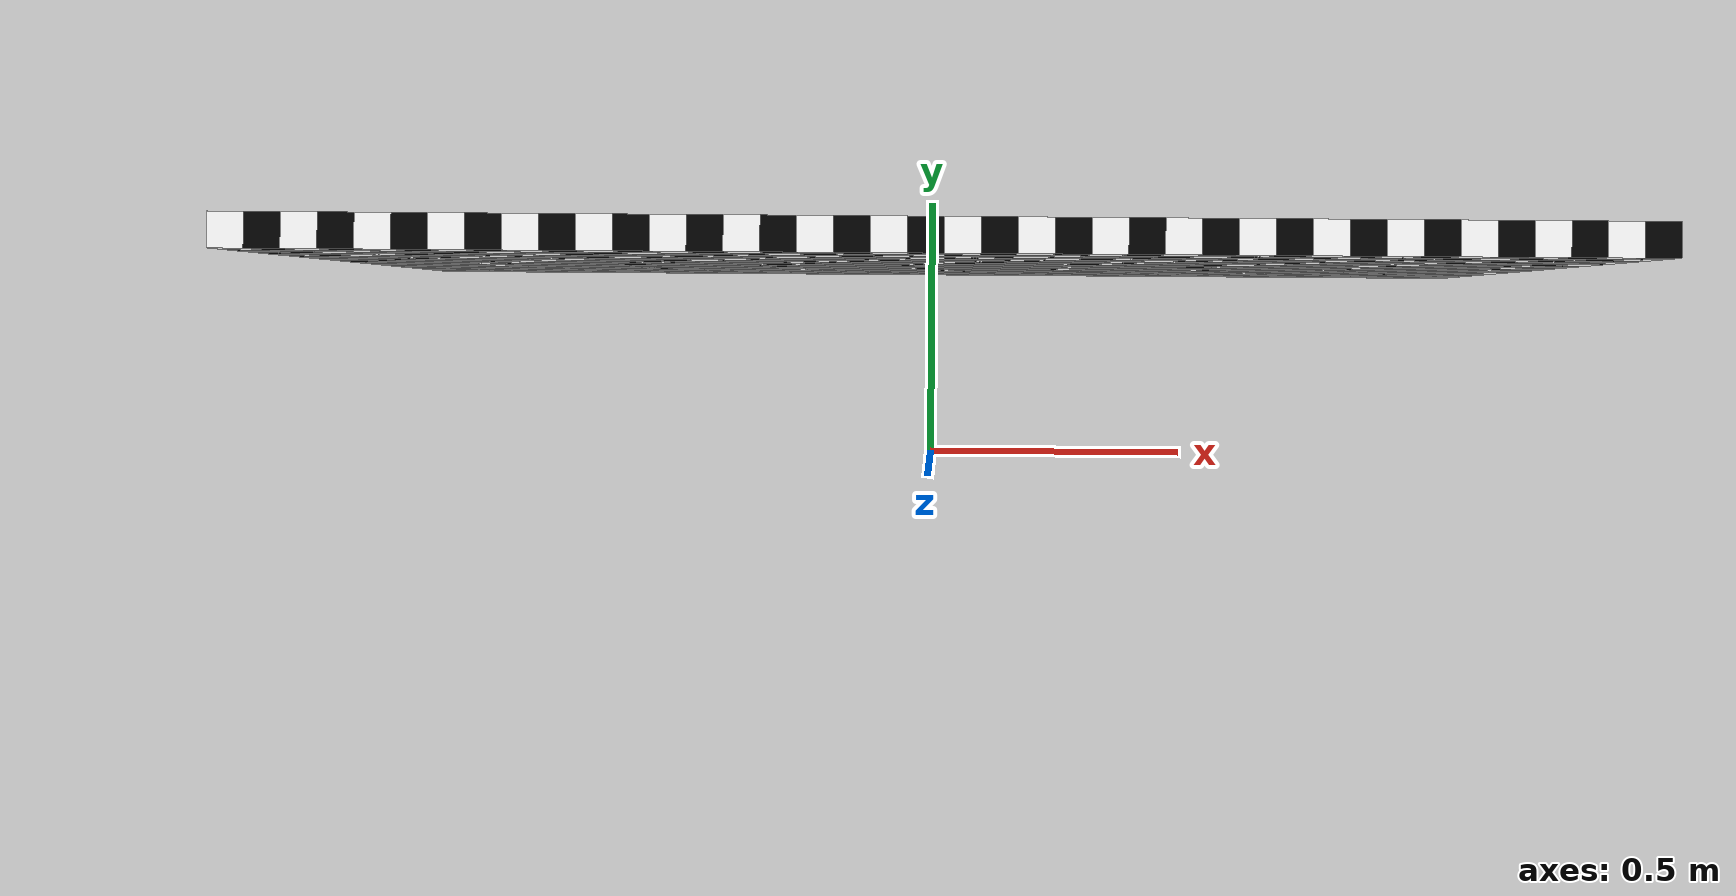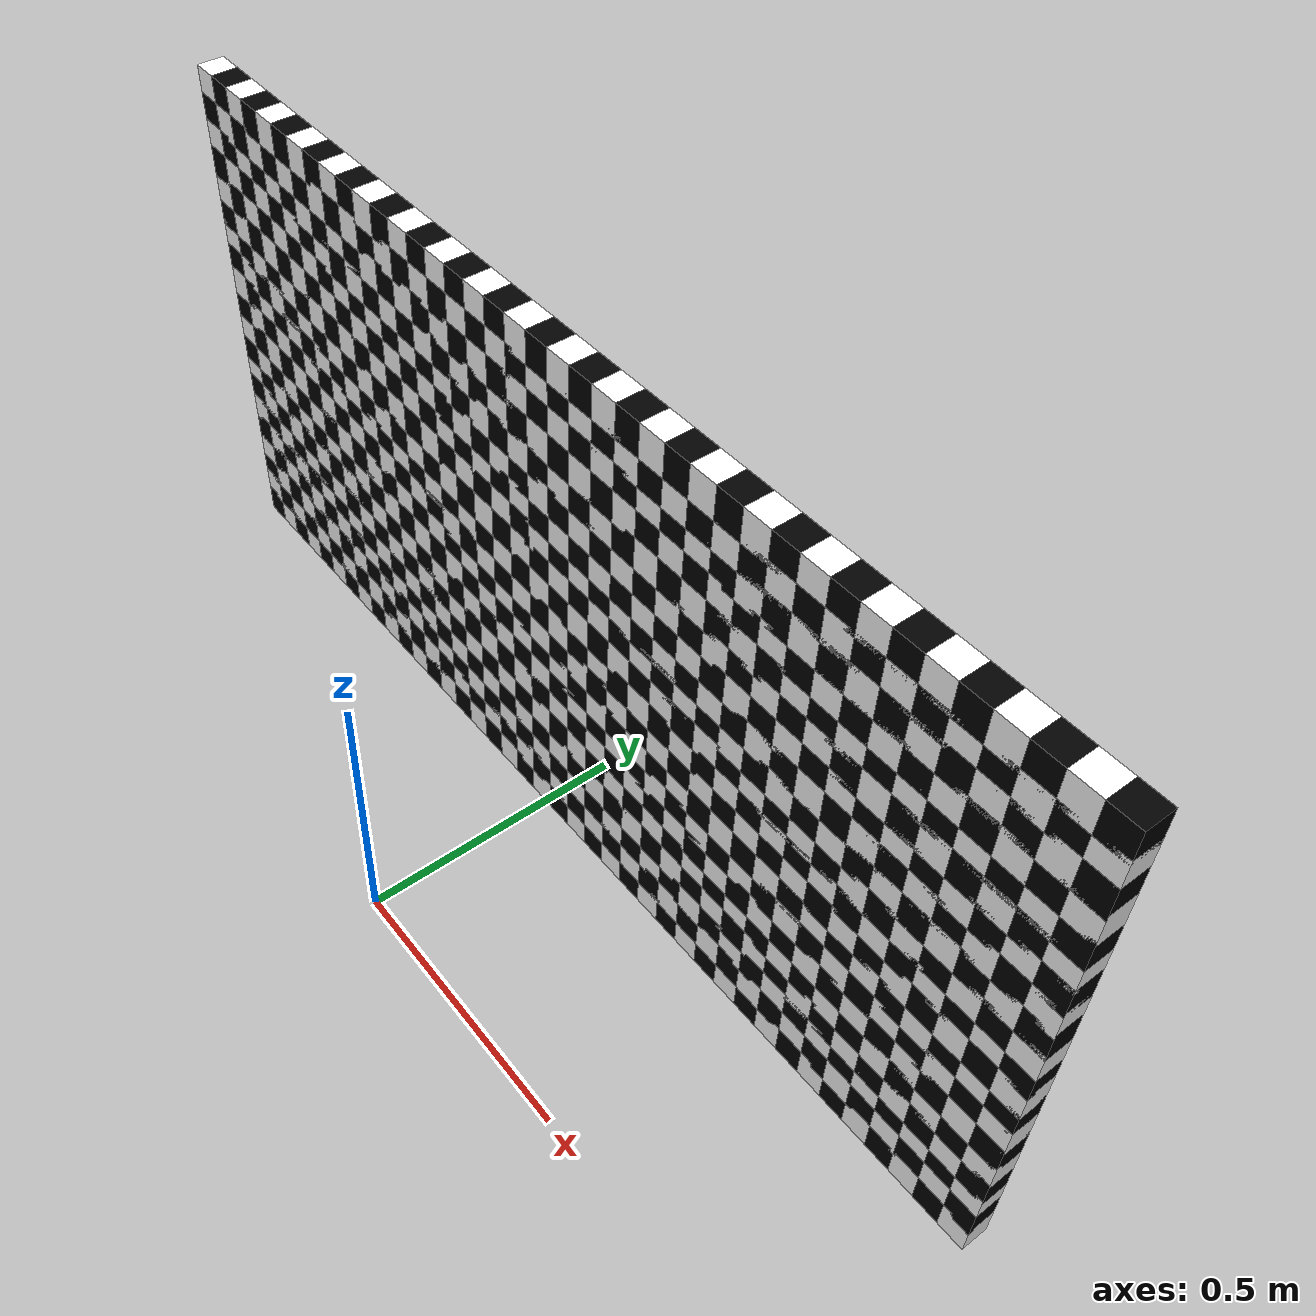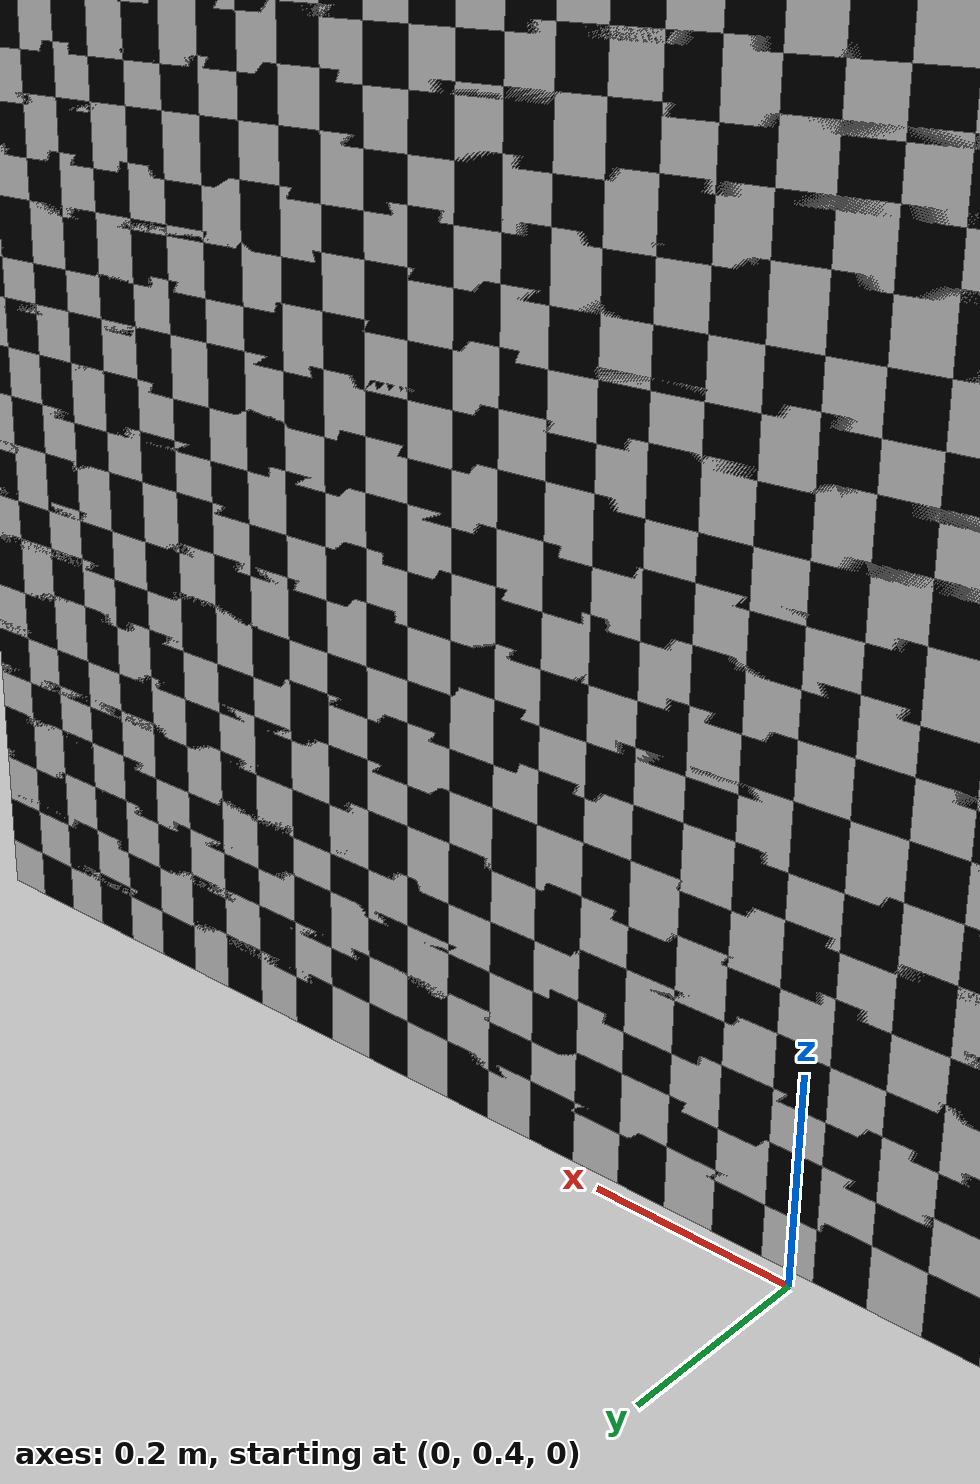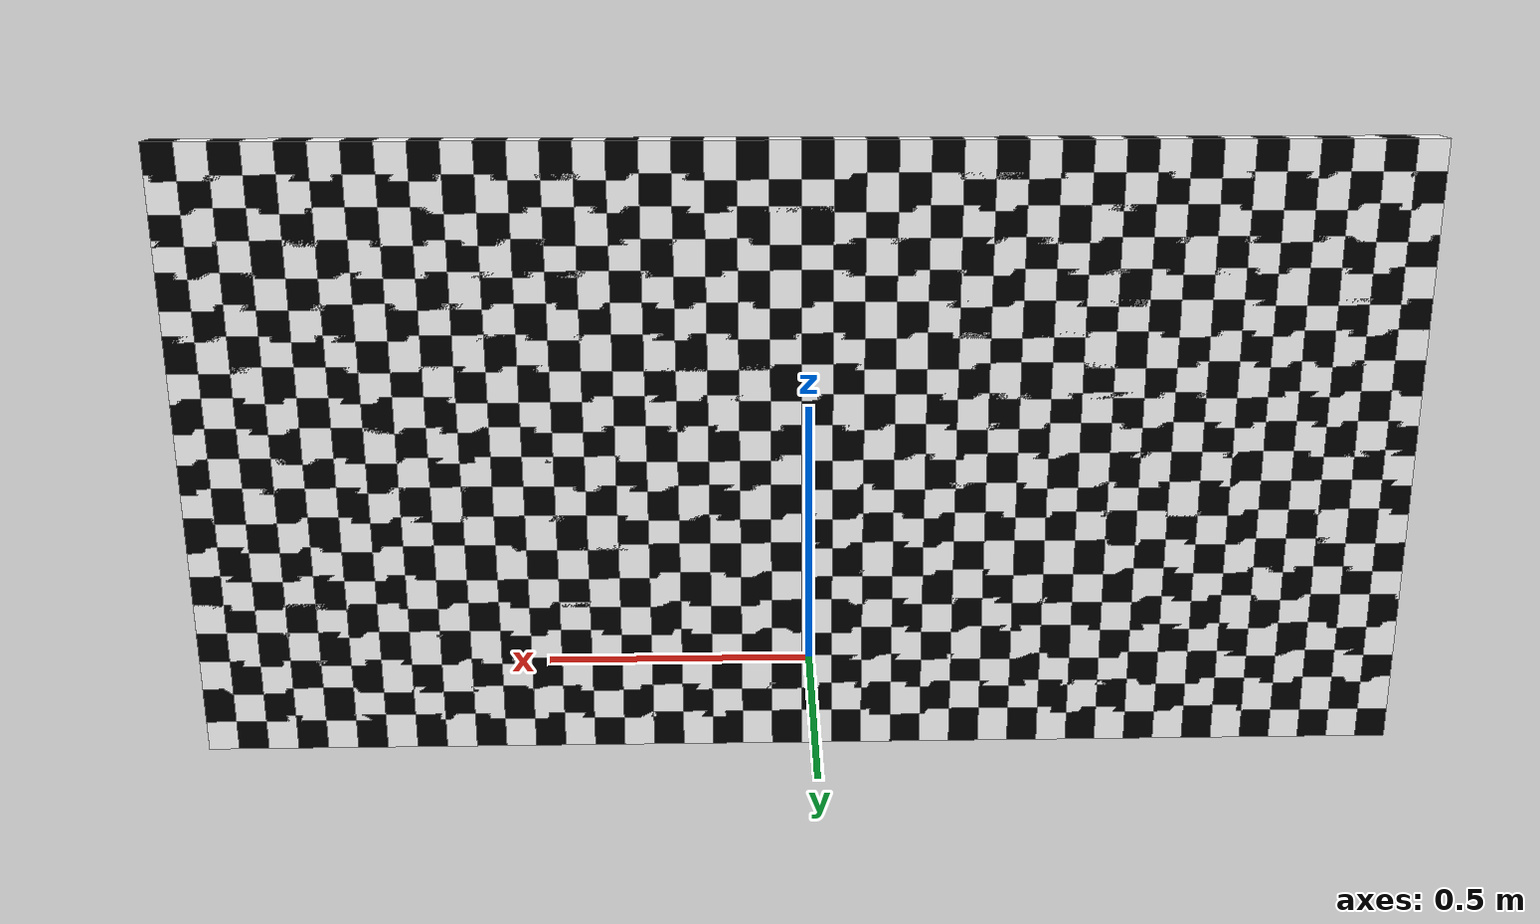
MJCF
<!-- This file was generated by angled_surface.py -->
<!-- It is not recommended to edit this file -->
<mujoco>
    <default>
        <geom density="100" friction=".5" rgba="1 .6 .8 1" />
    </default>
    <worldbody>
        <geom type="box" size=".025 .025 .03" pos="-0.95 0.38 1.0" euler="0.0 0 0" rgba="1 1 1 1" />
<geom type="box" size=".025 .025 .03" pos="-0.8999999999999999 0.38 1.0" euler="0.0 0 0" rgba="0 0 0 1" />
<geom type="box" size=".025 .025 .03" pos="-0.85 0.38 1.0" euler="0.0 0 0" rgba="1 1 1 1" />
<geom type="box" size=".025 .025 .03" pos="-0.7999999999999999 0.38 1.0" euler="0.0 0 0" rgba="0 0 0 1" />
<geom type="box" size=".025 .025 .03" pos="-0.75 0.38 1.0" euler="0.0 0 0" rgba="1 1 1 1" />
<geom type="box" size=".025 .025 .03" pos="-0.7 0.38 1.0" euler="0.0 0 0" rgba="0 0 0 1" />
<geom type="box" size=".025 .025 .03" pos="-0.6499999999999999 0.38 1.0" euler="0.0 0 0" rgba="1 1 1 1" />
<geom type="box" size=".025 .025 .03" pos="-0.5999999999999999 0.38 1.0" euler="0.0 0 0" rgba="0 0 0 1" />
<geom type="box" size=".025 .025 .03" pos="-0.5499999999999999 0.38 1.0" euler="0.0 0 0" rgba="1 1 1 1" />
<geom type="box" size=".025 .025 .03" pos="-0.49999999999999994 0.38 1.0" euler="0.0 0 0" rgba="0 0 0 1" />
<geom type="box" size=".025 .025 .03" pos="-0.44999999999999996 0.38 1.0" euler="0.0 0 0" rgba="1 1 1 1" />
<geom type="box" size=".025 .025 .03" pos="-0.3999999999999999 0.38 1.0" euler="0.0 0 0" rgba="0 0 0 1" />
<geom type="box" size=".025 .025 .03" pos="-0.34999999999999987 0.38 1.0" euler="0.0 0 0" rgba="1 1 1 1" />
<geom type="box" size=".025 .025 .03" pos="-0.29999999999999993 0.38 1.0" euler="0.0 0 0" rgba="0 0 0 1" />
<geom type="box" size=".025 .025 .03" pos="-0.2499999999999999 0.38 1.0" euler="0.0 0 0" rgba="1 1 1 1" />
<geom type="box" size=".025 .025 .03" pos="-0.19999999999999996 0.38 1.0" euler="0.0 0 0" rgba="0 0 0 1" />
<geom type="box" size=".025 .025 .03" pos="-0.1499999999999999 0.38 1.0" euler="0.0 0 0" rgba="1 1 1 1" />
<geom type="box" size=".025 .025 .03" pos="-0.09999999999999987 0.38 1.0" euler="0.0 0 0" rgba="0 0 0 1" />
<geom type="box" size=".025 .025 .03" pos="-0.04999999999999993 0.38 1.0" euler="0.0 0 0" rgba="1 1 1 1" />
<geom type="box" size=".025 .025 .03" pos="1.1102230246251565e-16 0.38 1.0" euler="0.0 0 0" rgba="0 0 0 1" />
<geom type="box" size=".025 .025 .03" pos="0.050000000000000044 0.38 1.0" euler="0.0 0 0" rgba="1 1 1 1" />
<geom type="box" size=".025 .025 .03" pos="0.10000000000000009 0.38 1.0" euler="0.0 0 0" rgba="0 0 0 1" />
<geom type="box" size=".025 .025 .03" pos="0.15000000000000013 0.38 1.0" euler="0.0 0 0" rgba="1 1 1 1" />
<geom type="box" size=".025 .025 .03" pos="0.20000000000000018 0.38 1.0" euler="0.0 0 0" rgba="0 0 0 1" />
<geom type="box" size=".025 .025 .03" pos="0.2500000000000002 0.38 1.0" euler="0.0 0 0" rgba="1 1 1 1" />
<geom type="box" size=".025 .025 .03" pos="0.30000000000000004 0.38 1.0" euler="0.0 0 0" rgba="0 0 0 1" />
<geom type="box" size=".025 .025 .03" pos="0.3500000000000001 0.38 1.0" euler="0.0 0 0" rgba="1 1 1 1" />
<geom type="box" size=".025 .025 .03" pos="0.40000000000000013 0.38 1.0" euler="0.0 0 0" rgba="0 0 0 1" />
<geom type="box" size=".025 .025 .03" pos="0.4500000000000002 0.38 1.0" euler="0.0 0 0" rgba="1 1 1 1" />
<geom type="box" size=".025 .025 .03" pos="0.5000000000000002 0.38 1.0" euler="0.0 0 0" rgba="0 0 0 1" />
<geom type="box" size=".025 .025 .03" pos="0.55 0.38 1.0" euler="0.0 0 0" rgba="1 1 1 1" />
<geom type="box" size=".025 .025 .03" pos="0.6000000000000001 0.38 1.0" euler="0.0 0 0" rgba="0 0 0 1" />
<geom type="box" size=".025 .025 .03" pos="0.6500000000000001 0.38 1.0" euler="0.0 0 0" rgba="1 1 1 1" />
<geom type="box" size=".025 .025 .03" pos="0.7000000000000002 0.38 1.0" euler="0.0 0 0" rgba="0 0 0 1" />
<geom type="box" size=".025 .025 .03" pos="0.7500000000000002 0.38 1.0" euler="0.0 0 0" rgba="1 1 1 1" />
<geom type="box" size=".025 .025 .03" pos="0.8 0.38 1.0" euler="0.0 0 0" rgba="0 0 0 1" />
<geom type="box" size=".025 .025 .03" pos="0.8500000000000001 0.38 1.0" euler="0.0 0 0" rgba="1 1 1 1" />
<geom type="box" size=".025 .025 .03" pos="0.9000000000000001 0.38 1.0" euler="0.0 0 0" rgba="0 0 0 1" />
<geom type="box" size=".025 .025 .03" pos="0.9500000000000002 0.38 1.0" euler="0.0 0 0" rgba="1 1 1 1" />
<geom type="box" size=".025 .025 .03" pos="1.0000000000000002 0.38 1.0" euler="0.0 0 0" rgba="0 0 0 1" />
<geom type="box" size=".025 .025 .03" pos="-0.95 0.38 0.95" euler="0.0 0 0" rgba="0 0 0 1" />
<geom type="box" size=".025 .025 .03" pos="-0.8999999999999999 0.38 0.95" euler="0.0 0 0" rgba="1 1 1 1" />
<geom type="box" size=".025 .025 .03" pos="-0.85 0.38 0.95" euler="0.0 0 0" rgba="0 0 0 1" />
<geom type="box" size=".025 .025 .03" pos="-0.7999999999999999 0.38 0.95" euler="0.0 0 0" rgba="1 1 1 1" />
<geom type="box" size=".025 .025 .03" pos="-0.75 0.38 0.95" euler="0.0 0 0" rgba="0 0 0 1" />
<geom type="box" size=".025 .025 .03" pos="-0.7 0.38 0.95" euler="0.0 0 0" rgba="1 1 1 1" />
<geom type="box" size=".025 .025 .03" pos="-0.6499999999999999 0.38 0.95" euler="0.0 0 0" rgba="0 0 0 1" />
<geom type="box" size=".025 .025 .03" pos="-0.5999999999999999 0.38 0.95" euler="0.0 0 0" rgba="1 1 1 1" />
<geom type="box" size=".025 .025 .03" pos="-0.5499999999999999 0.38 0.95" euler="0.0 0 0" rgba="0 0 0 1" />
<geom type="box" size=".025 .025 .03" pos="-0.49999999999999994 0.38 0.95" euler="0.0 0 0" rgba="1 1 1 1" />
<geom type="box" size=".025 .025 .03" pos="-0.44999999999999996 0.38 0.95" euler="0.0 0 0" rgba="0 0 0 1" />
<geom type="box" size=".025 .025 .03" pos="-0.3999999999999999 0.38 0.95" euler="0.0 0 0" rgba="1 1 1 1" />
<geom type="box" size=".025 .025 .03" pos="-0.34999999999999987 0.38 0.95" euler="0.0 0 0" rgba="0 0 0 1" />
<geom type="box" size=".025 .025 .03" pos="-0.29999999999999993 0.38 0.95" euler="0.0 0 0" rgba="1 1 1 1" />
<geom type="box" size=".025 .025 .03" pos="-0.2499999999999999 0.38 0.95" euler="0.0 0 0" rgba="0 0 0 1" />
<geom type="box" size=".025 .025 .03" pos="-0.19999999999999996 0.38 0.95" euler="0.0 0 0" rgba="1 1 1 1" />
<geom type="box" size=".025 .025 .03" pos="-0.1499999999999999 0.38 0.95" euler="0.0 0 0" rgba="0 0 0 1" />
<geom type="box" size=".025 .025 .03" pos="-0.09999999999999987 0.38 0.95" euler="0.0 0 0" rgba="1 1 1 1" />
<geom type="box" size=".025 .025 .03" pos="-0.04999999999999993 0.38 0.95" euler="0.0 0 0" rgba="0 0 0 1" />
<geom type="box" size=".025 .025 .03" pos="1.1102230246251565e-16 0.38 0.95" euler="0.0 0 0" rgba="1 1 1 1" />
<geom type="box" size=".025 .025 .03" pos="0.050000000000000044 0.38 0.95" euler="0.0 0 0" rgba="0 0 0 1" />
<geom type="box" size=".025 .025 .03" pos="0.10000000000000009 0.38 0.95" euler="0.0 0 0" rgba="1 1 1 1" />
<geom type="box" size=".025 .025 .03" pos="0.15000000000000013 0.38 0.95" euler="0.0 0 0" rgba="0 0 0 1" />
<geom type="box" size=".025 .025 .03" pos="0.20000000000000018 0.38 0.95" euler="0.0 0 0" rgba="1 1 1 1" />
<geom type="box" size=".025 .025 .03" pos="0.2500000000000002 0.38 0.95" euler="0.0 0 0" rgba="0 0 0 1" />
<geom type="box" size=".025 .025 .03" pos="0.30000000000000004 0.38 0.95" euler="0.0 0 0" rgba="1 1 1 1" />
<geom type="box" size=".025 .025 .03" pos="0.3500000000000001 0.38 0.95" euler="0.0 0 0" rgba="0 0 0 1" />
<geom type="box" size=".025 .025 .03" pos="0.40000000000000013 0.38 0.95" euler="0.0 0 0" rgba="1 1 1 1" />
<geom type="box" size=".025 .025 .03" pos="0.4500000000000002 0.38 0.95" euler="0.0 0 0" rgba="0 0 0 1" />
<geom type="box" size=".025 .025 .03" pos="0.5000000000000002 0.38 0.95" euler="0.0 0 0" rgba="1 1 1 1" />
<geom type="box" size=".025 .025 .03" pos="0.55 0.38 0.95" euler="0.0 0 0" rgba="0 0 0 1" />
<geom type="box" size=".025 .025 .03" pos="0.6000000000000001 0.38 0.95" euler="0.0 0 0" rgba="1 1 1 1" />
<geom type="box" size=".025 .025 .03" pos="0.6500000000000001 0.38 0.95" euler="0.0 0 0" rgba="0 0 0 1" />
<geom type="box" size=".025 .025 .03" pos="0.7000000000000002 0.38 0.95" euler="0.0 0 0" rgba="1 1 1 1" />
<geom type="box" size=".025 .025 .03" pos="0.7500000000000002 0.38 0.95" euler="0.0 0 0" rgba="0 0 0 1" />
<geom type="box" size=".025 .025 .03" pos="0.8 0.38 0.95" euler="0.0 0 0" rgba="1 1 1 1" />
<geom type="box" size=".025 .025 .03" pos="0.8500000000000001 0.38 0.95" euler="0.0 0 0" rgba="0 0 0 1" />
<geom type="box" size=".025 .025 .03" pos="0.9000000000000001 0.38 0.95" euler="0.0 0 0" rgba="1 1 1 1" />
<geom type="box" size=".025 .025 .03" pos="0.9500000000000002 0.38 0.95" euler="0.0 0 0" rgba="0 0 0 1" />
<geom type="box" size=".025 .025 .03" pos="1.0000000000000002 0.38 0.95" euler="0.0 0 0" rgba="1 1 1 1" />
<geom type="box" size=".025 .025 .03" pos="-0.95 0.38 0.9" euler="0.0 0 0" rgba="1 1 1 1" />
<geom type="box" size=".025 .025 .03" pos="-0.8999999999999999 0.38 0.9" euler="0.0 0 0" rgba="0 0 0 1" />
<geom type="box" size=".025 .025 .03" pos="-0.85 0.38 0.9" euler="0.0 0 0" rgba="1 1 1 1" />
<geom type="box" size=".025 .025 .03" pos="-0.7999999999999999 0.38 0.9" euler="0.0 0 0" rgba="0 0 0 1" />
<geom type="box" size=".025 .025 .03" pos="-0.75 0.38 0.9" euler="0.0 0 0" rgba="1 1 1 1" />
<geom type="box" size=".025 .025 .03" pos="-0.7 0.38 0.9" euler="0.0 0 0" rgba="0 0 0 1" />
<geom type="box" size=".025 .025 .03" pos="-0.6499999999999999 0.38 0.9" euler="0.0 0 0" rgba="1 1 1 1" />
<geom type="box" size=".025 .025 .03" pos="-0.5999999999999999 0.38 0.9" euler="0.0 0 0" rgba="0 0 0 1" />
<geom type="box" size=".025 .025 .03" pos="-0.5499999999999999 0.38 0.9" euler="0.0 0 0" rgba="1 1 1 1" />
<geom type="box" size=".025 .025 .03" pos="-0.49999999999999994 0.38 0.9" euler="0.0 0 0" rgba="0 0 0 1" />
<geom type="box" size=".025 .025 .03" pos="-0.44999999999999996 0.38 0.9" euler="0.0 0 0" rgba="1 1 1 1" />
<geom type="box" size=".025 .025 .03" pos="-0.3999999999999999 0.38 0.9" euler="0.0 0 0" rgba="0 0 0 1" />
<geom type="box" size=".025 .025 .03" pos="-0.34999999999999987 0.38 0.9" euler="0.0 0 0" rgba="1 1 1 1" />
<geom type="box" size=".025 .025 .03" pos="-0.29999999999999993 0.38 0.9" euler="0.0 0 0" rgba="0 0 0 1" />
<geom type="box" size=".025 .025 .03" pos="-0.2499999999999999 0.38 0.9" euler="0.0 0 0" rgba="1 1 1 1" />
<geom type="box" size=".025 .025 .03" pos="-0.19999999999999996 0.38 0.9" euler="0.0 0 0" rgba="0 0 0 1" />
<geom type="box" size=".025 .025 .03" pos="-0.1499999999999999 0.38 0.9" euler="0.0 0 0" rgba="1 1 1 1" />
<geom type="box" size=".025 .025 .03" pos="-0.09999999999999987 0.38 0.9" euler="0.0 0 0" rgba="0 0 0 1" />
<geom type="box" size=".025 .025 .03" pos="-0.04999999999999993 0.38 0.9" euler="0.0 0 0" rgba="1 1 1 1" />
<geom type="box" size=".025 .025 .03" pos="1.1102230246251565e-16 0.38 0.9" euler="0.0 0 0" rgba="0 0 0 1" />
<geom type="box" size=".025 .025 .03" pos="0.050000000000000044 0.38 0.9" euler="0.0 0 0" rgba="1 1 1 1" />
<geom type="box" size=".025 .025 .03" pos="0.10000000000000009 0.38 0.9" euler="0.0 0 0" rgba="0 0 0 1" />
<geom type="box" size=".025 .025 .03" pos="0.15000000000000013 0.38 0.9" euler="0.0 0 0" rgba="1 1 1 1" />
<geom type="box" size=".025 .025 .03" pos="0.20000000000000018 0.38 0.9" euler="0.0 0 0" rgba="0 0 0 1" />
<geom type="box" size=".025 .025 .03" pos="0.2500000000000002 0.38 0.9" euler="0.0 0 0" rgba="1 1 1 1" />
<geom type="box" size=".025 .025 .03" pos="0.30000000000000004 0.38 0.9" euler="0.0 0 0" rgba="0 0 0 1" />
<geom type="box" size=".025 .025 .03" pos="0.3500000000000001 0.38 0.9" euler="0.0 0 0" rgba="1 1 1 1" />
<geom type="box" size=".025 .025 .03" pos="0.40000000000000013 0.38 0.9" euler="0.0 0 0" rgba="0 0 0 1" />
<geom type="box" size=".025 .025 .03" pos="0.4500000000000002 0.38 0.9" euler="0.0 0 0" rgba="1 1 1 1" />
<geom type="box" size=".025 .025 .03" pos="0.5000000000000002 0.38 0.9" euler="0.0 0 0" rgba="0 0 0 1" />
<geom type="box" size=".025 .025 .03" pos="0.55 0.38 0.9" euler="0.0 0 0" rgba="1 1 1 1" />
<geom type="box" size=".025 .025 .03" pos="0.6000000000000001 0.38 0.9" euler="0.0 0 0" rgba="0 0 0 1" />
<geom type="box" size=".025 .025 .03" pos="0.6500000000000001 0.38 0.9" euler="0.0 0 0" rgba="1 1 1 1" />
<geom type="box" size=".025 .025 .03" pos="0.7000000000000002 0.38 0.9" euler="0.0 0 0" rgba="0 0 0 1" />
<geom type="box" size=".025 .025 .03" pos="0.7500000000000002 0.38 0.9" euler="0.0 0 0" rgba="1 1 1 1" />
<geom type="box" size=".025 .025 .03" pos="0.8 0.38 0.9" euler="0.0 0 0" rgba="0 0 0 1" />
<geom type="box" size=".025 .025 .03" pos="0.8500000000000001 0.38 0.9" euler="0.0 0 0" rgba="1 1 1 1" />
<geom type="box" size=".025 .025 .03" pos="0.9000000000000001 0.38 0.9" euler="0.0 0 0" rgba="0 0 0 1" />
<geom type="box" size=".025 .025 .03" pos="0.9500000000000002 0.38 0.9" euler="0.0 0 0" rgba="1 1 1 1" />
<geom type="box" size=".025 .025 .03" pos="1.0000000000000002 0.38 0.9" euler="0.0 0 0" rgba="0 0 0 1" />
<geom type="box" size=".025 .025 .03" pos="-0.95 0.38 0.85" euler="0.0 0 0" rgba="0 0 0 1" />
<geom type="box" size=".025 .025 .03" pos="-0.8999999999999999 0.38 0.85" euler="0.0 0 0" rgba="1 1 1 1" />
<geom type="box" size=".025 .025 .03" pos="-0.85 0.38 0.85" euler="0.0 0 0" rgba="0 0 0 1" />
<geom type="box" size=".025 .025 .03" pos="-0.7999999999999999 0.38 0.85" euler="0.0 0 0" rgba="1 1 1 1" />
<geom type="box" size=".025 .025 .03" pos="-0.75 0.38 0.85" euler="0.0 0 0" rgba="0 0 0 1" />
<geom type="box" size=".025 .025 .03" pos="-0.7 0.38 0.85" euler="0.0 0 0" rgba="1 1 1 1" />
<geom type="box" size=".025 .025 .03" pos="-0.6499999999999999 0.38 0.85" euler="0.0 0 0" rgba="0 0 0 1" />
<geom type="box" size=".025 .025 .03" pos="-0.5999999999999999 0.38 0.85" euler="0.0 0 0" rgba="1 1 1 1" />
<geom type="box" size=".025 .025 .03" pos="-0.5499999999999999 0.38 0.85" euler="0.0 0 0" rgba="0 0 0 1" />
<geom type="box" size=".025 .025 .03" pos="-0.49999999999999994 0.38 0.85" euler="0.0 0 0" rgba="1 1 1 1" />
<geom type="box" size=".025 .025 .03" pos="-0.44999999999999996 0.38 0.85" euler="0.0 0 0" rgba="0 0 0 1" />
<geom type="box" size=".025 .025 .03" pos="-0.3999999999999999 0.38 0.85" euler="0.0 0 0" rgba="1 1 1 1" />
<geom type="box" size=".025 .025 .03" pos="-0.34999999999999987 0.38 0.85" euler="0.0 0 0" rgba="0 0 0 1" />
<geom type="box" size=".025 .025 .03" pos="-0.29999999999999993 0.38 0.85" euler="0.0 0 0" rgba="1 1 1 1" />
<geom type="box" size=".025 .025 .03" pos="-0.2499999999999999 0.38 0.85" euler="0.0 0 0" rgba="0 0 0 1" />
<geom type="box" size=".025 .025 .03" pos="-0.19999999999999996 0.38 0.85" euler="0.0 0 0" rgba="1 1 1 1" />
<geom type="box" size=".025 .025 .03" pos="-0.1499999999999999 0.38 0.85" euler="0.0 0 0" rgba="0 0 0 1" />
<geom type="box" size=".025 .025 .03" pos="-0.09999999999999987 0.38 0.85" euler="0.0 0 0" rgba="1 1 1 1" />
<geom type="box" size=".025 .025 .03" pos="-0.04999999999999993 0.38 0.85" euler="0.0 0 0" rgba="0 0 0 1" />
<geom type="box" size=".025 .025 .03" pos="1.1102230246251565e-16 0.38 0.85" euler="0.0 0 0" rgba="1 1 1 1" />
<geom type="box" size=".025 .025 .03" pos="0.050000000000000044 0.38 0.85" euler="0.0 0 0" rgba="0 0 0 1" />
<geom type="box" size=".025 .025 .03" pos="0.10000000000000009 0.38 0.85" euler="0.0 0 0" rgba="1 1 1 1" />
<geom type="box" size=".025 .025 .03" pos="0.15000000000000013 0.38 0.85" euler="0.0 0 0" rgba="0 0 0 1" />
<geom type="box" size=".025 .025 .03" pos="0.20000000000000018 0.38 0.85" euler="0.0 0 0" rgba="1 1 1 1" />
<geom type="box" size=".025 .025 .03" pos="0.2500000000000002 0.38 0.85" euler="0.0 0 0" rgba="0 0 0 1" />
<geom type="box" size=".025 .025 .03" pos="0.30000000000000004 0.38 0.85" euler="0.0 0 0" rgba="1 1 1 1" />
<geom type="box" size=".025 .025 .03" pos="0.3500000000000001 0.38 0.85" euler="0.0 0 0" rgba="0 0 0 1" />
<geom type="box" size=".025 .025 .03" pos="0.40000000000000013 0.38 0.85" euler="0.0 0 0" rgba="1 1 1 1" />
<geom type="box" size=".025 .025 .03" pos="0.4500000000000002 0.38 0.85" euler="0.0 0 0" rgba="0 0 0 1" />
<geom type="box" size=".025 .025 .03" pos="0.5000000000000002 0.38 0.85" euler="0.0 0 0" rgba="1 1 1 1" />
<geom type="box" size=".025 .025 .03" pos="0.55 0.38 0.85" euler="0.0 0 0" rgba="0 0 0 1" />
<geom type="box" size=".025 .025 .03" pos="0.6000000000000001 0.38 0.85" euler="0.0 0 0" rgba="1 1 1 1" />
<geom type="box" size=".025 .025 .03" pos="0.6500000000000001 0.38 0.85" euler="0.0 0 0" rgba="0 0 0 1" />
<geom type="box" size=".025 .025 .03" pos="0.7000000000000002 0.38 0.85" euler="0.0 0 0" rgba="1 1 1 1" />
<geom type="box" size=".025 .025 .03" pos="0.7500000000000002 0.38 0.85" euler="0.0 0 0" rgba="0 0 0 1" />
<geom type="box" size=".025 .025 .03" pos="0.8 0.38 0.85" euler="0.0 0 0" rgba="1 1 1 1" />
<geom type="box" size=".025 .025 .03" pos="0.8500000000000001 0.38 0.85" euler="0.0 0 0" rgba="0 0 0 1" />
<geom type="box" size=".025 .025 .03" pos="0.9000000000000001 0.38 0.85" euler="0.0 0 0" rgba="1 1 1 1" />
<geom type="box" size=".025 .025 .03" pos="0.9500000000000002 0.38 0.85" euler="0.0 0 0" rgba="0 0 0 1" />
<geom type="box" size=".025 .025 .03" pos="1.0000000000000002 0.38 0.85" euler="0.0 0 0" rgba="1 1 1 1" />
<geom type="box" size=".025 .025 .03" pos="-0.95 0.38 0.8" euler="0.0 0 0" rgba="1 1 1 1" />
<geom type="box" size=".025 .025 .03" pos="-0.8999999999999999 0.38 0.8" euler="0.0 0 0" rgba="0 0 0 1" />
<geom type="box" size=".025 .025 .03" pos="-0.85 0.38 0.8" euler="0.0 0 0" rgba="1 1 1 1" />
<geom type="box" size=".025 .025 .03" pos="-0.7999999999999999 0.38 0.8" euler="0.0 0 0" rgba="0 0 0 1" />
<geom type="box" size=".025 .025 .03" pos="-0.75 0.38 0.8" euler="0.0 0 0" rgba="1 1 1 1" />
<geom type="box" size=".025 .025 .03" pos="-0.7 0.38 0.8" euler="0.0 0 0" rgba="0 0 0 1" />
<geom type="box" size=".025 .025 .03" pos="-0.6499999999999999 0.38 0.8" euler="0.0 0 0" rgba="1 1 1 1" />
<geom type="box" size=".025 .025 .03" pos="-0.5999999999999999 0.38 0.8" euler="0.0 0 0" rgba="0 0 0 1" />
<geom type="box" size=".025 .025 .03" pos="-0.5499999999999999 0.38 0.8" euler="0.0 0 0" rgba="1 1 1 1" />
<geom type="box" size=".025 .025 .03" pos="-0.49999999999999994 0.38 0.8" euler="0.0 0 0" rgba="0 0 0 1" />
<geom type="box" size=".025 .025 .03" pos="-0.44999999999999996 0.38 0.8" euler="0.0 0 0" rgba="1 1 1 1" />
<geom type="box" size=".025 .025 .03" pos="-0.3999999999999999 0.38 0.8" euler="0.0 0 0" rgba="0 0 0 1" />
<geom type="box" size=".025 .025 .03" pos="-0.34999999999999987 0.38 0.8" euler="0.0 0 0" rgba="1 1 1 1" />
<geom type="box" size=".025 .025 .03" pos="-0.29999999999999993 0.38 0.8" euler="0.0 0 0" rgba="0 0 0 1" />
<geom type="box" size=".025 .025 .03" pos="-0.2499999999999999 0.38 0.8" euler="0.0 0 0" rgba="1 1 1 1" />
<geom type="box" size=".025 .025 .03" pos="-0.19999999999999996 0.38 0.8" euler="0.0 0 0" rgba="0 0 0 1" />
<geom type="box" size=".025 .025 .03" pos="-0.1499999999999999 0.38 0.8" euler="0.0 0 0" rgba="1 1 1 1" />
<geom type="box" size=".025 .025 .03" pos="-0.09999999999999987 0.38 0.8" euler="0.0 0 0" rgba="0 0 0 1" />
<geom type="box" size=".025 .025 .03" pos="-0.04999999999999993 0.38 0.8" euler="0.0 0 0" rgba="1 1 1 1" />
<geom type="box" size=".025 .025 .03" pos="1.1102230246251565e-16 0.38 0.8" euler="0.0 0 0" rgba="0 0 0 1" />
<geom type="box" size=".025 .025 .03" pos="0.050000000000000044 0.38 0.8" euler="0.0 0 0" rgba="1 1 1 1" />
<geom type="box" size=".025 .025 .03" pos="0.10000000000000009 0.38 0.8" euler="0.0 0 0" rgba="0 0 0 1" />
<geom type="box" size=".025 .025 .03" pos="0.15000000000000013 0.38 0.8" euler="0.0 0 0" rgba="1 1 1 1" />
<geom type="box" size=".025 .025 .03" pos="0.20000000000000018 0.38 0.8" euler="0.0 0 0" rgba="0 0 0 1" />
<geom type="box" size=".025 .025 .03" pos="0.2500000000000002 0.38 0.8" euler="0.0 0 0" rgba="1 1 1 1" />
<geom type="box" size=".025 .025 .03" pos="0.30000000000000004 0.38 0.8" euler="0.0 0 0" rgba="0 0 0 1" />
<geom type="box" size=".025 .025 .03" pos="0.3500000000000001 0.38 0.8" euler="0.0 0 0" rgba="1 1 1 1" />
<geom type="box" size=".025 .025 .03" pos="0.40000000000000013 0.38 0.8" euler="0.0 0 0" rgba="0 0 0 1" />
<geom type="box" size=".025 .025 .03" pos="0.4500000000000002 0.38 0.8" euler="0.0 0 0" rgba="1 1 1 1" />
<geom type="box" size=".025 .025 .03" pos="0.5000000000000002 0.38 0.8" euler="0.0 0 0" rgba="0 0 0 1" />
<geom type="box" size=".025 .025 .03" pos="0.55 0.38 0.8" euler="0.0 0 0" rgba="1 1 1 1" />
<geom type="box" size=".025 .025 .03" pos="0.6000000000000001 0.38 0.8" euler="0.0 0 0" rgba="0 0 0 1" />
<geom type="box" size=".025 .025 .03" pos="0.6500000000000001 0.38 0.8" euler="0.0 0 0" rgba="1 1 1 1" />
<geom type="box" size=".025 .025 .03" pos="0.7000000000000002 0.38 0.8" euler="0.0 0 0" rgba="0 0 0 1" />
<geom type="box" size=".025 .025 .03" pos="0.7500000000000002 0.38 0.8" euler="0.0 0 0" rgba="1 1 1 1" />
<geom type="box" size=".025 .025 .03" pos="0.8 0.38 0.8" euler="0.0 0 0" rgba="0 0 0 1" />
<geom type="box" size=".025 .025 .03" pos="0.8500000000000001 0.38 0.8" euler="0.0 0 0" rgba="1 1 1 1" />
<geom type="box" size=".025 .025 .03" pos="0.9000000000000001 0.38 0.8" euler="0.0 0 0" rgba="0 0 0 1" />
<geom type="box" size=".025 .025 .03" pos="0.9500000000000002 0.38 0.8" euler="0.0 0 0" rgba="1 1 1 1" />
<geom type="box" size=".025 .025 .03" pos="1.0000000000000002 0.38 0.8" euler="0.0 0 0" rgba="0 0 0 1" />
<geom type="box" size=".025 .025 .03" pos="-0.95 0.38 0.75" euler="0.0 0 0" rgba="0 0 0 1" />
<geom type="box" size=".025 .025 .03" pos="-0.8999999999999999 0.38 0.75" euler="0.0 0 0" rgba="1 1 1 1" />
<geom type="box" size=".025 .025 .03" pos="-0.85 0.38 0.75" euler="0.0 0 0" rgba="0 0 0 1" />
<geom type="box" size=".025 .025 .03" pos="-0.7999999999999999 0.38 0.75" euler="0.0 0 0" rgba="1 1 1 1" />
<geom type="box" size=".025 .025 .03" pos="-0.75 0.38 0.75" euler="0.0 0 0" rgba="0 0 0 1" />
<geom type="box" size=".025 .025 .03" pos="-0.7 0.38 0.75" euler="0.0 0 0" rgba="1 1 1 1" />
<geom type="box" size=".025 .025 .03" pos="-0.6499999999999999 0.38 0.75" euler="0.0 0 0" rgba="0 0 0 1" />
<geom type="box" size=".025 .025 .03" pos="-0.5999999999999999 0.38 0.75" euler="0.0 0 0" rgba="1 1 1 1" />
<geom type="box" size=".025 .025 .03" pos="-0.5499999999999999 0.38 0.75" euler="0.0 0 0" rgba="0 0 0 1" />
<geom type="box" size=".025 .025 .03" pos="-0.49999999999999994 0.38 0.75" euler="0.0 0 0" rgba="1 1 1 1" />
<geom type="box" size=".025 .025 .03" pos="-0.44999999999999996 0.38 0.75" euler="0.0 0 0" rgba="0 0 0 1" />
<geom type="box" size=".025 .025 .03" pos="-0.3999999999999999 0.38 0.75" euler="0.0 0 0" rgba="1 1 1 1" />
<geom type="box" size=".025 .025 .03" pos="-0.34999999999999987 0.38 0.75" euler="0.0 0 0" rgba="0 0 0 1" />
<geom type="box" size=".025 .025 .03" pos="-0.29999999999999993 0.38 0.75" euler="0.0 0 0" rgba="1 1 1 1" />
<geom type="box" size=".025 .025 .03" pos="-0.2499999999999999 0.38 0.75" euler="0.0 0 0" rgba="0 0 0 1" />
<geom type="box" size=".025 .025 .03" pos="-0.19999999999999996 0.38 0.75" euler="0.0 0 0" rgba="1 1 1 1" />
<geom type="box" size=".025 .025 .03" pos="-0.1499999999999999 0.38 0.75" euler="0.0 0 0" rgba="0 0 0 1" />
<geom type="box" size=".025 .025 .03" pos="-0.09999999999999987 0.38 0.75" euler="0.0 0 0" rgba="1 1 1 1" />
<geom type="box" size=".025 .025 .03" pos="-0.04999999999999993 0.38 0.75" euler="0.0 0 0" rgba="0 0 0 1" />
<geom type="box" size=".025 .025 .03" pos="1.1102230246251565e-16 0.38 0.75" euler="0.0 0 0" rgba="1 1 1 1" />
<geom type="box" size=".025 .025 .03" pos="0.050000000000000044 0.38 0.75" euler="0.0 0 0" rgba="0 0 0 1" />
<geom type="box" size=".025 .025 .03" pos="0.10000000000000009 0.38 0.75" euler="0.0 0 0" rgba="1 1 1 1" />
<geom type="box" size=".025 .025 .03" pos="0.15000000000000013 0.38 0.75" euler="0.0 0 0" rgba="0 0 0 1" />
<geom type="box" size=".025 .025 .03" pos="0.20000000000000018 0.38 0.75" euler="0.0 0 0" rgba="1 1 1 1" />
<geom type="box" size=".025 .025 .03" pos="0.2500000000000002 0.38 0.75" euler="0.0 0 0" rgba="0 0 0 1" />
<geom type="box" size=".025 .025 .03" pos="0.30000000000000004 0.38 0.75" euler="0.0 0 0" rgba="1 1 1 1" />
<geom type="box" size=".025 .025 .03" pos="0.3500000000000001 0.38 0.75" euler="0.0 0 0" rgba="0 0 0 1" />
<geom type="box" size=".025 .025 .03" pos="0.40000000000000013 0.38 0.75" euler="0.0 0 0" rgba="1 1 1 1" />
<geom type="box" size=".025 .025 .03" pos="0.4500000000000002 0.38 0.75" euler="0.0 0 0" rgba="0 0 0 1" />
<geom type="box" size=".025 .025 .03" pos="0.5000000000000002 0.38 0.75" euler="0.0 0 0" rgba="1 1 1 1" />
<geom type="box" size=".025 .025 .03" pos="0.55 0.38 0.75" euler="0.0 0 0" rgba="0 0 0 1" />
<geom type="box" size=".025 .025 .03" pos="0.6000000000000001 0.38 0.75" euler="0.0 0 0" rgba="1 1 1 1" />
<geom type="box" size=".025 .025 .03" pos="0.6500000000000001 0.38 0.75" euler="0.0 0 0" rgba="0 0 0 1" />
<geom type="box" size=".025 .025 .03" pos="0.7000000000000002 0.38 0.75" euler="0.0 0 0" rgba="1 1 1 1" />
<geom type="box" size=".025 .025 .03" pos="0.7500000000000002 0.38 0.75" euler="0.0 0 0" rgba="0 0 0 1" />
<geom type="box" size=".025 .025 .03" pos="0.8 0.38 0.75" euler="0.0 0 0" rgba="1 1 1 1" />
<geom type="box" size=".025 .025 .03" pos="0.8500000000000001 0.38 0.75" euler="0.0 0 0" rgba="0 0 0 1" />
<geom type="box" size=".025 .025 .03" pos="0.9000000000000001 0.38 0.75" euler="0.0 0 0" rgba="1 1 1 1" />
<geom type="box" size=".025 .025 .03" pos="0.9500000000000002 0.38 0.75" euler="0.0 0 0" rgba="0 0 0 1" />
<geom type="box" size=".025 .025 .03" pos="1.0000000000000002 0.38 0.75" euler="0.0 0 0" rgba="1 1 1 1" />
<geom type="box" size=".025 .025 .03" pos="-0.95 0.38 0.7" euler="0.0 0 0" rgba="1 1 1 1" />
<geom type="box" size=".025 .025 .03" pos="-0.8999999999999999 0.38 0.7" euler="0.0 0 0" rgba="0 0 0 1" />
<geom type="box" size=".025 .025 .03" pos="-0.85 0.38 0.7" euler="0.0 0 0" rgba="1 1 1 1" />
<geom type="box" size=".025 .025 .03" pos="-0.7999999999999999 0.38 0.7" euler="0.0 0 0" rgba="0 0 0 1" />
<geom type="box" size=".025 .025 .03" pos="-0.75 0.38 0.7" euler="0.0 0 0" rgba="1 1 1 1" />
<geom type="box" size=".025 .025 .03" pos="-0.7 0.38 0.7" euler="0.0 0 0" rgba="0 0 0 1" />
<geom type="box" size=".025 .025 .03" pos="-0.6499999999999999 0.38 0.7" euler="0.0 0 0" rgba="1 1 1 1" />
<geom type="box" size=".025 .025 .03" pos="-0.5999999999999999 0.38 0.7" euler="0.0 0 0" rgba="0 0 0 1" />
<geom type="box" size=".025 .025 .03" pos="-0.5499999999999999 0.38 0.7" euler="0.0 0 0" rgba="1 1 1 1" />
<geom type="box" size=".025 .025 .03" pos="-0.49999999999999994 0.38 0.7" euler="0.0 0 0" rgba="0 0 0 1" />
<geom type="box" size=".025 .025 .03" pos="-0.44999999999999996 0.38 0.7" euler="0.0 0 0" rgba="1 1 1 1" />
<geom type="box" size=".025 .025 .03" pos="-0.3999999999999999 0.38 0.7" euler="0.0 0 0" rgba="0 0 0 1" />
<geom type="box" size=".025 .025 .03" pos="-0.34999999999999987 0.38 0.7" euler="0.0 0 0" rgba="1 1 1 1" />
<geom type="box" size=".025 .025 .03" pos="-0.29999999999999993 0.38 0.7" euler="0.0 0 0" rgba="0 0 0 1" />
<geom type="box" size=".025 .025 .03" pos="-0.2499999999999999 0.38 0.7" euler="0.0 0 0" rgba="1 1 1 1" />
<geom type="box" size=".025 .025 .03" pos="-0.19999999999999996 0.38 0.7" euler="0.0 0 0" rgba="0 0 0 1" />
<geom type="box" size=".025 .025 .03" pos="-0.1499999999999999 0.38 0.7" euler="0.0 0 0" rgba="1 1 1 1" />
<geom type="box" size=".025 .025 .03" pos="-0.09999999999999987 0.38 0.7" euler="0.0 0 0" rgba="0 0 0 1" />
<geom type="box" size=".025 .025 .03" pos="-0.04999999999999993 0.38 0.7" euler="0.0 0 0" rgba="1 1 1 1" />
<geom type="box" size=".025 .025 .03" pos="1.1102230246251565e-16 0.38 0.7" euler="0.0 0 0" rgba="0 0 0 1" />
<geom type="box" size=".025 .025 .03" pos="0.050000000000000044 0.38 0.7" euler="0.0 0 0" rgba="1 1 1 1" />
<geom type="box" size=".025 .025 .03" pos="0.10000000000000009 0.38 0.7" euler="0.0 0 0" rgba="0 0 0 1" />
<geom type="box" size=".025 .025 .03" pos="0.15000000000000013 0.38 0.7" euler="0.0 0 0" rgba="1 1 1 1" />
<geom type="box" size=".025 .025 .03" pos="0.20000000000000018 0.38 0.7" euler="0.0 0 0" rgba="0 0 0 1" />
<geom type="box" size=".025 .025 .03" pos="0.2500000000000002 0.38 0.7" euler="0.0 0 0" rgba="1 1 1 1" />
<geom type="box" size=".025 .025 .03" pos="0.30000000000000004 0.38 0.7" euler="0.0 0 0" rgba="0 0 0 1" />
<geom type="box" size=".025 .025 .03" pos="0.3500000000000001 0.38 0.7" euler="0.0 0 0" rgba="1 1 1 1" />
<geom type="box" size=".025 .025 .03" pos="0.40000000000000013 0.38 0.7" euler="0.0 0 0" rgba="0 0 0 1" />
<geom type="box" size=".025 .025 .03" pos="0.4500000000000002 0.38 0.7" euler="0.0 0 0" rgba="1 1 1 1" />
<geom type="box" size=".025 .025 .03" pos="0.5000000000000002 0.38 0.7" euler="0.0 0 0" rgba="0 0 0 1" />
<geom type="box" size=".025 .025 .03" pos="0.55 0.38 0.7" euler="0.0 0 0" rgba="1 1 1 1" />
<geom type="box" size=".025 .025 .03" pos="0.6000000000000001 0.38 0.7" euler="0.0 0 0" rgba="0 0 0 1" />
<geom type="box" size=".025 .025 .03" pos="0.6500000000000001 0.38 0.7" euler="0.0 0 0" rgba="1 1 1 1" />
<geom type="box" size=".025 .025 .03" pos="0.7000000000000002 0.38 0.7" euler="0.0 0 0" rgba="0 0 0 1" />
<geom type="box" size=".025 .025 .03" pos="0.7500000000000002 0.38 0.7" euler="0.0 0 0" rgba="1 1 1 1" />
<geom type="box" size=".025 .025 .03" pos="0.8 0.38 0.7" euler="0.0 0 0" rgba="0 0 0 1" />
<geom type="box" size=".025 .025 .03" pos="0.8500000000000001 0.38 0.7" euler="0.0 0 0" rgba="1 1 1 1" />
<geom type="box" size=".025 .025 .03" pos="0.9000000000000001 0.38 0.7" euler="0.0 0 0" rgba="0 0 0 1" />
<geom type="box" size=".025 .025 .03" pos="0.9500000000000002 0.38 0.7" euler="0.0 0 0" rgba="1 1 1 1" />
<geom type="box" size=".025 .025 .03" pos="1.0000000000000002 0.38 0.7" euler="0.0 0 0" rgba="0 0 0 1" />
<geom type="box" size=".025 .025 .03" pos="-0.95 0.38 0.6499999999999999" euler="0.0 0 0" rgba="0 0 0 1" />
<geom type="box" size=".025 .025 .03" pos="-0.8999999999999999 0.38 0.6499999999999999" euler="0.0 0 0" rgba="1 1 1 1" />
<geom type="box" size=".025 .025 .03" pos="-0.85 0.38 0.6499999999999999" euler="0.0 0 0" rgba="0 0 0 1" />
<geom type="box" size=".025 .025 .03" pos="-0.7999999999999999 0.38 0.6499999999999999" euler="0.0 0 0" rgba="1 1 1 1" />
<geom type="box" size=".025 .025 .03" pos="-0.75 0.38 0.6499999999999999" euler="0.0 0 0" rgba="0 0 0 1" />
<geom type="box" size=".025 .025 .03" pos="-0.7 0.38 0.6499999999999999" euler="0.0 0 0" rgba="1 1 1 1" />
<geom type="box" size=".025 .025 .03" pos="-0.6499999999999999 0.38 0.6499999999999999" euler="0.0 0 0" rgba="0 0 0 1" />
<geom type="box" size=".025 .025 .03" pos="-0.5999999999999999 0.38 0.6499999999999999" euler="0.0 0 0" rgba="1 1 1 1" />
<geom type="box" size=".025 .025 .03" pos="-0.5499999999999999 0.38 0.6499999999999999" euler="0.0 0 0" rgba="0 0 0 1" />
<geom type="box" size=".025 .025 .03" pos="-0.49999999999999994 0.38 0.6499999999999999" euler="0.0 0 0" rgba="1 1 1 1" />
<geom type="box" size=".025 .025 .03" pos="-0.44999999999999996 0.38 0.6499999999999999" euler="0.0 0 0" rgba="0 0 0 1" />
<geom type="box" size=".025 .025 .03" pos="-0.3999999999999999 0.38 0.6499999999999999" euler="0.0 0 0" rgba="1 1 1 1" />
<geom type="box" size=".025 .025 .03" pos="-0.34999999999999987 0.38 0.6499999999999999" euler="0.0 0 0" rgba="0 0 0 1" />
<geom type="box" size=".025 .025 .03" pos="-0.29999999999999993 0.38 0.6499999999999999" euler="0.0 0 0" rgba="1 1 1 1" />
<geom type="box" size=".025 .025 .03" pos="-0.2499999999999999 0.38 0.6499999999999999" euler="0.0 0 0" rgba="0 0 0 1" />
<geom type="box" size=".025 .025 .03" pos="-0.19999999999999996 0.38 0.6499999999999999" euler="0.0 0 0" rgba="1 1 1 1" />
<geom type="box" size=".025 .025 .03" pos="-0.1499999999999999 0.38 0.6499999999999999" euler="0.0 0 0" rgba="0 0 0 1" />
<geom type="box" size=".025 .025 .03" pos="-0.09999999999999987 0.38 0.6499999999999999" euler="0.0 0 0" rgba="1 1 1 1" />
<geom type="box" size=".025 .025 .03" pos="-0.04999999999999993 0.38 0.6499999999999999" euler="0.0 0 0" rgba="0 0 0 1" />
<geom type="box" size=".025 .025 .03" pos="1.1102230246251565e-16 0.38 0.6499999999999999" euler="0.0 0 0" rgba="1 1 1 1" />
<geom type="box" size=".025 .025 .03" pos="0.050000000000000044 0.38 0.6499999999999999" euler="0.0 0 0" rgba="0 0 0 1" />
<geom type="box" size=".025 .025 .03" pos="0.10000000000000009 0.38 0.6499999999999999" euler="0.0 0 0" rgba="1 1 1 1" />
<geom type="box" size=".025 .025 .03" pos="0.15000000000000013 0.38 0.6499999999999999" euler="0.0 0 0" rgba="0 0 0 1" />
<geom type="box" size=".025 .025 .03" pos="0.20000000000000018 0.38 0.6499999999999999" euler="0.0 0 0" rgba="1 1 1 1" />
<geom type="box" size=".025 .025 .03" pos="0.2500000000000002 0.38 0.6499999999999999" euler="0.0 0 0" rgba="0 0 0 1" />
<geom type="box" size=".025 .025 .03" pos="0.30000000000000004 0.38 0.6499999999999999" euler="0.0 0 0" rgba="1 1 1 1" />
<geom type="box" size=".025 .025 .03" pos="0.3500000000000001 0.38 0.6499999999999999" euler="0.0 0 0" rgba="0 0 0 1" />
<geom type="box" size=".025 .025 .03" pos="0.40000000000000013 0.38 0.6499999999999999" euler="0.0 0 0" rgba="1 1 1 1" />
<geom type="box" size=".025 .025 .03" pos="0.4500000000000002 0.38 0.6499999999999999" euler="0.0 0 0" rgba="0 0 0 1" />
<geom type="box" size=".025 .025 .03" pos="0.5000000000000002 0.38 0.6499999999999999" euler="0.0 0 0" rgba="1 1 1 1" />
<geom type="box" size=".025 .025 .03" pos="0.55 0.38 0.6499999999999999" euler="0.0 0 0" rgba="0 0 0 1" />
<geom type="box" size=".025 .025 .03" pos="0.6000000000000001 0.38 0.6499999999999999" euler="0.0 0 0" rgba="1 1 1 1" />
<geom type="box" size=".025 .025 .03" pos="0.6500000000000001 0.38 0.6499999999999999" euler="0.0 0 0" rgba="0 0 0 1" />
<geom type="box" size=".025 .025 .03" pos="0.7000000000000002 0.38 0.6499999999999999" euler="0.0 0 0" rgba="1 1 1 1" />
<geom type="box" size=".025 .025 .03" pos="0.7500000000000002 0.38 0.6499999999999999" euler="0.0 0 0" rgba="0 0 0 1" />
<geom type="box" size=".025 .025 .03" pos="0.8 0.38 0.6499999999999999" euler="0.0 0 0" rgba="1 1 1 1" />
<geom type="box" size=".025 .025 .03" pos="0.8500000000000001 0.38 0.6499999999999999" euler="0.0 0 0" rgba="0 0 0 1" />
<geom type="box" size=".025 .025 .03" pos="0.9000000000000001 0.38 0.6499999999999999" euler="0.0 0 0" rgba="1 1 1 1" />
<geom type="box" size=".025 .025 .03" pos="0.9500000000000002 0.38 0.6499999999999999" euler="0.0 0 0" rgba="0 0 0 1" />
<geom type="box" size=".025 .025 .03" pos="1.0000000000000002 0.38 0.6499999999999999" euler="0.0 0 0" rgba="1 1 1 1" />
<geom type="box" size=".025 .025 .03" pos="-0.95 0.38 0.6" euler="0.0 0 0" rgba="1 1 1 1" />
<geom type="box" size=".025 .025 .03" pos="-0.8999999999999999 0.38 0.6" euler="0.0 0 0" rgba="0 0 0 1" />
<geom type="box" size=".025 .025 .03" pos="-0.85 0.38 0.6" euler="0.0 0 0" rgba="1 1 1 1" />
<geom type="box" size=".025 .025 .03" pos="-0.7999999999999999 0.38 0.6" euler="0.0 0 0" rgba="0 0 0 1" />
<geom type="box" size=".025 .025 .03" pos="-0.75 0.38 0.6" euler="0.0 0 0" rgba="1 1 1 1" />
<geom type="box" size=".025 .025 .03" pos="-0.7 0.38 0.6" euler="0.0 0 0" rgba="0 0 0 1" />
<geom type="box" size=".025 .025 .03" pos="-0.6499999999999999 0.38 0.6" euler="0.0 0 0" rgba="1 1 1 1" />
<geom type="box" size=".025 .025 .03" pos="-0.5999999999999999 0.38 0.6" euler="0.0 0 0" rgba="0 0 0 1" />
<geom type="box" size=".025 .025 .03" pos="-0.5499999999999999 0.38 0.6" euler="0.0 0 0" rgba="1 1 1 1" />
<geom type="box" size=".025 .025 .03" pos="-0.49999999999999994 0.38 0.6" euler="0.0 0 0" rgba="0 0 0 1" />
<geom type="box" size=".025 .025 .03" pos="-0.44999999999999996 0.38 0.6" euler="0.0 0 0" rgba="1 1 1 1" />
<geom type="box" size=".025 .025 .03" pos="-0.3999999999999999 0.38 0.6" euler="0.0 0 0" rgba="0 0 0 1" />
<geom type="box" size=".025 .025 .03" pos="-0.34999999999999987 0.38 0.6" euler="0.0 0 0" rgba="1 1 1 1" />
<geom type="box" size=".025 .025 .03" pos="-0.29999999999999993 0.38 0.6" euler="0.0 0 0" rgba="0 0 0 1" />
<geom type="box" size=".025 .025 .03" pos="-0.2499999999999999 0.38 0.6" euler="0.0 0 0" rgba="1 1 1 1" />
<geom type="box" size=".025 .025 .03" pos="-0.19999999999999996 0.38 0.6" euler="0.0 0 0" rgba="0 0 0 1" />
<geom type="box" size=".025 .025 .03" pos="-0.1499999999999999 0.38 0.6" euler="0.0 0 0" rgba="1 1 1 1" />
<geom type="box" size=".025 .025 .03" pos="-0.09999999999999987 0.38 0.6" euler="0.0 0 0" rgba="0 0 0 1" />
<geom type="box" size=".025 .025 .03" pos="-0.04999999999999993 0.38 0.6" euler="0.0 0 0" rgba="1 1 1 1" />
<geom type="box" size=".025 .025 .03" pos="1.1102230246251565e-16 0.38 0.6" euler="0.0 0 0" rgba="0 0 0 1" />
<geom type="box" size=".025 .025 .03" pos="0.050000000000000044 0.38 0.6" euler="0.0 0 0" rgba="1 1 1 1" />
<geom type="box" size=".025 .025 .03" pos="0.10000000000000009 0.38 0.6" euler="0.0 0 0" rgba="0 0 0 1" />
<geom type="box" size=".025 .025 .03" pos="0.15000000000000013 0.38 0.6" euler="0.0 0 0" rgba="1 1 1 1" />
<geom type="box" size=".025 .025 .03" pos="0.20000000000000018 0.38 0.6" euler="0.0 0 0" rgba="0 0 0 1" />
<geom type="box" size=".025 .025 .03" pos="0.2500000000000002 0.38 0.6" euler="0.0 0 0" rgba="1 1 1 1" />
<geom type="box" size=".025 .025 .03" pos="0.30000000000000004 0.38 0.6" euler="0.0 0 0" rgba="0 0 0 1" />
<geom type="box" size=".025 .025 .03" pos="0.3500000000000001 0.38 0.6" euler="0.0 0 0" rgba="1 1 1 1" />
<geom type="box" size=".025 .025 .03" pos="0.40000000000000013 0.38 0.6" euler="0.0 0 0" rgba="0 0 0 1" />
<geom type="box" size=".025 .025 .03" pos="0.4500000000000002 0.38 0.6" euler="0.0 0 0" rgba="1 1 1 1" />
<geom type="box" size=".025 .025 .03" pos="0.5000000000000002 0.38 0.6" euler="0.0 0 0" rgba="0 0 0 1" />
<geom type="box" size=".025 .025 .03" pos="0.55 0.38 0.6" euler="0.0 0 0" rgba="1 1 1 1" />
<geom type="box" size=".025 .025 .03" pos="0.6000000000000001 0.38 0.6" euler="0.0 0 0" rgba="0 0 0 1" />
<geom type="box" size=".025 .025 .03" pos="0.6500000000000001 0.38 0.6" euler="0.0 0 0" rgba="1 1 1 1" />
<geom type="box" size=".025 .025 .03" pos="0.7000000000000002 0.38 0.6" euler="0.0 0 0" rgba="0 0 0 1" />
<geom type="box" size=".025 .025 .03" pos="0.7500000000000002 0.38 0.6" euler="0.0 0 0" rgba="1 1 1 1" />
<geom type="box" size=".025 .025 .03" pos="0.8 0.38 0.6" euler="0.0 0 0" rgba="0 0 0 1" />
<geom type="box" size=".025 .025 .03" pos="0.8500000000000001 0.38 0.6" euler="0.0 0 0" rgba="1 1 1 1" />
<geom type="box" size=".025 .025 .03" pos="0.9000000000000001 0.38 0.6" euler="0.0 0 0" rgba="0 0 0 1" />
<geom type="box" size=".025 .025 .03" pos="0.9500000000000002 0.38 0.6" euler="0.0 0 0" rgba="1 1 1 1" />
<geom type="box" size=".025 .025 .03" pos="1.0000000000000002 0.38 0.6" euler="0.0 0 0" rgba="0 0 0 1" />
<geom type="box" size=".025 .025 .03" pos="-0.95 0.38 0.55" euler="0.0 0 0" rgba="0 0 0 1" />
<geom type="box" size=".025 .025 .03" pos="-0.8999999999999999 0.38 0.55" euler="0.0 0 0" rgba="1 1 1 1" />
<geom type="box" size=".025 .025 .03" pos="-0.85 0.38 0.55" euler="0.0 0 0" rgba="0 0 0 1" />
<geom type="box" size=".025 .025 .03" pos="-0.7999999999999999 0.38 0.55" euler="0.0 0 0" rgba="1 1 1 1" />
<geom type="box" size=".025 .025 .03" pos="-0.75 0.38 0.55" euler="0.0 0 0" rgba="0 0 0 1" />
<geom type="box" size=".025 .025 .03" pos="-0.7 0.38 0.55" euler="0.0 0 0" rgba="1 1 1 1" />
<geom type="box" size=".025 .025 .03" pos="-0.6499999999999999 0.38 0.55" euler="0.0 0 0" rgba="0 0 0 1" />
<geom type="box" size=".025 .025 .03" pos="-0.5999999999999999 0.38 0.55" euler="0.0 0 0" rgba="1 1 1 1" />
<geom type="box" size=".025 .025 .03" pos="-0.5499999999999999 0.38 0.55" euler="0.0 0 0" rgba="0 0 0 1" />
<geom type="box" size=".025 .025 .03" pos="-0.49999999999999994 0.38 0.55" euler="0.0 0 0" rgba="1 1 1 1" />
<geom type="box" size=".025 .025 .03" pos="-0.44999999999999996 0.38 0.55" euler="0.0 0 0" rgba="0 0 0 1" />
<geom type="box" size=".025 .025 .03" pos="-0.3999999999999999 0.38 0.55" euler="0.0 0 0" rgba="1 1 1 1" />
<geom type="box" size=".025 .025 .03" pos="-0.34999999999999987 0.38 0.55" euler="0.0 0 0" rgba="0 0 0 1" />
<geom type="box" size=".025 .025 .03" pos="-0.29999999999999993 0.38 0.55" euler="0.0 0 0" rgba="1 1 1 1" />
<geom type="box" size=".025 .025 .03" pos="-0.2499999999999999 0.38 0.55" euler="0.0 0 0" rgba="0 0 0 1" />
<geom type="box" size=".025 .025 .03" pos="-0.19999999999999996 0.38 0.55" euler="0.0 0 0" rgba="1 1 1 1" />
<geom type="box" size=".025 .025 .03" pos="-0.1499999999999999 0.38 0.55" euler="0.0 0 0" rgba="0 0 0 1" />
<geom type="box" size=".025 .025 .03" pos="-0.09999999999999987 0.38 0.55" euler="0.0 0 0" rgba="1 1 1 1" />
<geom type="box" size=".025 .025 .03" pos="-0.04999999999999993 0.38 0.55" euler="0.0 0 0" rgba="0 0 0 1" />
<geom type="box" size=".025 .025 .03" pos="1.1102230246251565e-16 0.38 0.55" euler="0.0 0 0" rgba="1 1 1 1" />
<geom type="box" size=".025 .025 .03" pos="0.050000000000000044 0.38 0.55" euler="0.0 0 0" rgba="0 0 0 1" />
<geom type="box" size=".025 .025 .03" pos="0.10000000000000009 0.38 0.55" euler="0.0 0 0" rgba="1 1 1 1" />
<geom type="box" size=".025 .025 .03" pos="0.15000000000000013 0.38 0.55" euler="0.0 0 0" rgba="0 0 0 1" />
<geom type="box" size=".025 .025 .03" pos="0.20000000000000018 0.38 0.55" euler="0.0 0 0" rgba="1 1 1 1" />
<geom type="box" size=".025 .025 .03" pos="0.2500000000000002 0.38 0.55" euler="0.0 0 0" rgba="0 0 0 1" />
<geom type="box" size=".025 .025 .03" pos="0.30000000000000004 0.38 0.55" euler="0.0 0 0" rgba="1 1 1 1" />
<geom type="box" size=".025 .025 .03" pos="0.3500000000000001 0.38 0.55" euler="0.0 0 0" rgba="0 0 0 1" />
<geom type="box" size=".025 .025 .03" pos="0.40000000000000013 0.38 0.55" euler="0.0 0 0" rgba="1 1 1 1" />
<geom type="box" size=".025 .025 .03" pos="0.4500000000000002 0.38 0.55" euler="0.0 0 0" rgba="0 0 0 1" />
<geom type="box" size=".025 .025 .03" pos="0.5000000000000002 0.38 0.55" euler="0.0 0 0" rgba="1 1 1 1" />
<geom type="box" size=".025 .025 .03" pos="0.55 0.38 0.55" euler="0.0 0 0" rgba="0 0 0 1" />
<geom type="box" size=".025 .025 .03" pos="0.6000000000000001 0.38 0.55" euler="0.0 0 0" rgba="1 1 1 1" />
<geom type="box" size=".025 .025 .03" pos="0.6500000000000001 0.38 0.55" euler="0.0 0 0" rgba="0 0 0 1" />
<geom type="box" size=".025 .025 .03" pos="0.7000000000000002 0.38 0.55" euler="0.0 0 0" rgba="1 1 1 1" />
<geom type="box" size=".025 .025 .03" pos="0.7500000000000002 0.38 0.55" euler="0.0 0 0" rgba="0 0 0 1" />
<geom type="box" size=".025 .025 .03" pos="0.8 0.38 0.55" euler="0.0 0 0" rgba="1 1 1 1" />
<geom type="box" size=".025 .025 .03" pos="0.8500000000000001 0.38 0.55" euler="0.0 0 0" rgba="0 0 0 1" />
<geom type="box" size=".025 .025 .03" pos="0.9000000000000001 0.38 0.55" euler="0.0 0 0" rgba="1 1 1 1" />
<geom type="box" size=".025 .025 .03" pos="0.9500000000000002 0.38 0.55" euler="0.0 0 0" rgba="0 0 0 1" />
<geom type="box" size=".025 .025 .03" pos="1.0000000000000002 0.38 0.55" euler="0.0 0 0" rgba="1 1 1 1" />
<geom type="box" size=".025 .025 .03" pos="-0.95 0.38 0.5" euler="0.0 0 0" rgba="1 1 1 1" />
<geom type="box" size=".025 .025 .03" pos="-0.8999999999999999 0.38 0.5" euler="0.0 0 0" rgba="0 0 0 1" />
<geom type="box" size=".025 .025 .03" pos="-0.85 0.38 0.5" euler="0.0 0 0" rgba="1 1 1 1" />
<geom type="box" size=".025 .025 .03" pos="-0.7999999999999999 0.38 0.5" euler="0.0 0 0" rgba="0 0 0 1" />
<geom type="box" size=".025 .025 .03" pos="-0.75 0.38 0.5" euler="0.0 0 0" rgba="1 1 1 1" />
<geom type="box" size=".025 .025 .03" pos="-0.7 0.38 0.5" euler="0.0 0 0" rgba="0 0 0 1" />
<geom type="box" size=".025 .025 .03" pos="-0.6499999999999999 0.38 0.5" euler="0.0 0 0" rgba="1 1 1 1" />
<geom type="box" size=".025 .025 .03" pos="-0.5999999999999999 0.38 0.5" euler="0.0 0 0" rgba="0 0 0 1" />
<geom type="box" size=".025 .025 .03" pos="-0.5499999999999999 0.38 0.5" euler="0.0 0 0" rgba="1 1 1 1" />
<geom type="box" size=".025 .025 .03" pos="-0.49999999999999994 0.38 0.5" euler="0.0 0 0" rgba="0 0 0 1" />
<geom type="box" size=".025 .025 .03" pos="-0.44999999999999996 0.38 0.5" euler="0.0 0 0" rgba="1 1 1 1" />
<geom type="box" size=".025 .025 .03" pos="-0.3999999999999999 0.38 0.5" euler="0.0 0 0" rgba="0 0 0 1" />
<geom type="box" size=".025 .025 .03" pos="-0.34999999999999987 0.38 0.5" euler="0.0 0 0" rgba="1 1 1 1" />
<geom type="box" size=".025 .025 .03" pos="-0.29999999999999993 0.38 0.5" euler="0.0 0 0" rgba="0 0 0 1" />
<geom type="box" size=".025 .025 .03" pos="-0.2499999999999999 0.38 0.5" euler="0.0 0 0" rgba="1 1 1 1" />
<geom type="box" size=".025 .025 .03" pos="-0.19999999999999996 0.38 0.5" euler="0.0 0 0" rgba="0 0 0 1" />
<geom type="box" size=".025 .025 .03" pos="-0.1499999999999999 0.38 0.5" euler="0.0 0 0" rgba="1 1 1 1" />
<geom type="box" size=".025 .025 .03" pos="-0.09999999999999987 0.38 0.5" euler="0.0 0 0" rgba="0 0 0 1" />
<geom type="box" size=".025 .025 .03" pos="-0.04999999999999993 0.38 0.5" euler="0.0 0 0" rgba="1 1 1 1" />
<geom type="box" size=".025 .025 .03" pos="1.1102230246251565e-16 0.38 0.5" euler="0.0 0 0" rgba="0 0 0 1" />
<geom type="box" size=".025 .025 .03" pos="0.050000000000000044 0.38 0.5" euler="0.0 0 0" rgba="1 1 1 1" />
<geom type="box" size=".025 .025 .03" pos="0.10000000000000009 0.38 0.5" euler="0.0 0 0" rgba="0 0 0 1" />
<geom type="box" size=".025 .025 .03" pos="0.15000000000000013 0.38 0.5" euler="0.0 0 0" rgba="1 1 1 1" />
<geom type="box" size=".025 .025 .03" pos="0.20000000000000018 0.38 0.5" euler="0.0 0 0" rgba="0 0 0 1" />
<geom type="box" size=".025 .025 .03" pos="0.2500000000000002 0.38 0.5" euler="0.0 0 0" rgba="1 1 1 1" />
<geom type="box" size=".025 .025 .03" pos="0.30000000000000004 0.38 0.5" euler="0.0 0 0" rgba="0 0 0 1" />
<geom type="box" size=".025 .025 .03" pos="0.3500000000000001 0.38 0.5" euler="0.0 0 0" rgba="1 1 1 1" />
<geom type="box" size=".025 .025 .03" pos="0.40000000000000013 0.38 0.5" euler="0.0 0 0" rgba="0 0 0 1" />
<geom type="box" size=".025 .025 .03" pos="0.4500000000000002 0.38 0.5" euler="0.0 0 0" rgba="1 1 1 1" />
<geom type="box" size=".025 .025 .03" pos="0.5000000000000002 0.38 0.5" euler="0.0 0 0" rgba="0 0 0 1" />
<geom type="box" size=".025 .025 .03" pos="0.55 0.38 0.5" euler="0.0 0 0" rgba="1 1 1 1" />
<geom type="box" size=".025 .025 .03" pos="0.6000000000000001 0.38 0.5" euler="0.0 0 0" rgba="0 0 0 1" />
<geom type="box" size=".025 .025 .03" pos="0.6500000000000001 0.38 0.5" euler="0.0 0 0" rgba="1 1 1 1" />
<geom type="box" size=".025 .025 .03" pos="0.7000000000000002 0.38 0.5" euler="0.0 0 0" rgba="0 0 0 1" />
<geom type="box" size=".025 .025 .03" pos="0.7500000000000002 0.38 0.5" euler="0.0 0 0" rgba="1 1 1 1" />
<geom type="box" size=".025 .025 .03" pos="0.8 0.38 0.5" euler="0.0 0 0" rgba="0 0 0 1" />
<geom type="box" size=".025 .025 .03" pos="0.8500000000000001 0.38 0.5" euler="0.0 0 0" rgba="1 1 1 1" />
<geom type="box" size=".025 .025 .03" pos="0.9000000000000001 0.38 0.5" euler="0.0 0 0" rgba="0 0 0 1" />
<geom type="box" size=".025 .025 .03" pos="0.9500000000000002 0.38 0.5" euler="0.0 0 0" rgba="1 1 1 1" />
<geom type="box" size=".025 .025 .03" pos="1.0000000000000002 0.38 0.5" euler="0.0 0 0" rgba="0 0 0 1" />
<geom type="box" size=".025 .025 .03" pos="-0.95 0.38 0.44999999999999996" euler="0.0 0 0" rgba="0 0 0 1" />
<geom type="box" size=".025 .025 .03" pos="-0.8999999999999999 0.38 0.44999999999999996" euler="0.0 0 0" rgba="1 1 1 1" />
<geom type="box" size=".025 .025 .03" pos="-0.85 0.38 0.44999999999999996" euler="0.0 0 0" rgba="0 0 0 1" />
<geom type="box" size=".025 .025 .03" pos="-0.7999999999999999 0.38 0.44999999999999996" euler="0.0 0 0" rgba="1 1 1 1" />
<geom type="box" size=".025 .025 .03" pos="-0.75 0.38 0.44999999999999996" euler="0.0 0 0" rgba="0 0 0 1" />
<geom type="box" size=".025 .025 .03" pos="-0.7 0.38 0.44999999999999996" euler="0.0 0 0" rgba="1 1 1 1" />
<geom type="box" size=".025 .025 .03" pos="-0.6499999999999999 0.38 0.44999999999999996" euler="0.0 0 0" rgba="0 0 0 1" />
<geom type="box" size=".025 .025 .03" pos="-0.5999999999999999 0.38 0.44999999999999996" euler="0.0 0 0" rgba="1 1 1 1" />
<geom type="box" size=".025 .025 .03" pos="-0.5499999999999999 0.38 0.44999999999999996" euler="0.0 0 0" rgba="0 0 0 1" />
<geom type="box" size=".025 .025 .03" pos="-0.49999999999999994 0.38 0.44999999999999996" euler="0.0 0 0" rgba="1 1 1 1" />
<geom type="box" size=".025 .025 .03" pos="-0.44999999999999996 0.38 0.44999999999999996" euler="0.0 0 0" rgba="0 0 0 1" />
<geom type="box" size=".025 .025 .03" pos="-0.3999999999999999 0.38 0.44999999999999996" euler="0.0 0 0" rgba="1 1 1 1" />
<geom type="box" size=".025 .025 .03" pos="-0.34999999999999987 0.38 0.44999999999999996" euler="0.0 0 0" rgba="0 0 0 1" />
<geom type="box" size=".025 .025 .03" pos="-0.29999999999999993 0.38 0.44999999999999996" euler="0.0 0 0" rgba="1 1 1 1" />
<geom type="box" size=".025 .025 .03" pos="-0.2499999999999999 0.38 0.44999999999999996" euler="0.0 0 0" rgba="0 0 0 1" />
<geom type="box" size=".025 .025 .03" pos="-0.19999999999999996 0.38 0.44999999999999996" euler="0.0 0 0" rgba="1 1 1 1" />
<geom type="box" size=".025 .025 .03" pos="-0.1499999999999999 0.38 0.44999999999999996" euler="0.0 0 0" rgba="0 0 0 1" />
<geom type="box" size=".025 .025 .03" pos="-0.09999999999999987 0.38 0.44999999999999996" euler="0.0 0 0" rgba="1 1 1 1" />
<geom type="box" size=".025 .025 .03" pos="-0.04999999999999993 0.38 0.44999999999999996" euler="0.0 0 0" rgba="0 0 0 1" />
<geom type="box" size=".025 .025 .03" pos="1.1102230246251565e-16 0.38 0.44999999999999996" euler="0.0 0 0" rgba="1 1 1 1" />
<geom type="box" size=".025 .025 .03" pos="0.050000000000000044 0.38 0.44999999999999996" euler="0.0 0 0" rgba="0 0 0 1" />
<geom type="box" size=".025 .025 .03" pos="0.10000000000000009 0.38 0.44999999999999996" euler="0.0 0 0" rgba="1 1 1 1" />
<geom type="box" size=".025 .025 .03" pos="0.15000000000000013 0.38 0.44999999999999996" euler="0.0 0 0" rgba="0 0 0 1" />
<geom type="box" size=".025 .025 .03" pos="0.20000000000000018 0.38 0.44999999999999996" euler="0.0 0 0" rgba="1 1 1 1" />
<geom type="box" size=".025 .025 .03" pos="0.2500000000000002 0.38 0.44999999999999996" euler="0.0 0 0" rgba="0 0 0 1" />
<geom type="box" size=".025 .025 .03" pos="0.30000000000000004 0.38 0.44999999999999996" euler="0.0 0 0" rgba="1 1 1 1" />
<geom type="box" size=".025 .025 .03" pos="0.3500000000000001 0.38 0.44999999999999996" euler="0.0 0 0" rgba="0 0 0 1" />
<geom type="box" size=".025 .025 .03" pos="0.40000000000000013 0.38 0.44999999999999996" euler="0.0 0 0" rgba="1 1 1 1" />
<geom type="box" size=".025 .025 .03" pos="0.4500000000000002 0.38 0.44999999999999996" euler="0.0 0 0" rgba="0 0 0 1" />
<geom type="box" size=".025 .025 .03" pos="0.5000000000000002 0.38 0.44999999999999996" euler="0.0 0 0" rgba="1 1 1 1" />
<geom type="box" size=".025 .025 .03" pos="0.55 0.38 0.44999999999999996" euler="0.0 0 0" rgba="0 0 0 1" />
<geom type="box" size=".025 .025 .03" pos="0.6000000000000001 0.38 0.44999999999999996" euler="0.0 0 0" rgba="1 1 1 1" />
<geom type="box" size=".025 .025 .03" pos="0.6500000000000001 0.38 0.44999999999999996" euler="0.0 0 0" rgba="0 0 0 1" />
<geom type="box" size=".025 .025 .03" pos="0.7000000000000002 0.38 0.44999999999999996" euler="0.0 0 0" rgba="1 1 1 1" />
<geom type="box" size=".025 .025 .03" pos="0.7500000000000002 0.38 0.44999999999999996" euler="0.0 0 0" rgba="0 0 0 1" />
<geom type="box" size=".025 .025 .03" pos="0.8 0.38 0.44999999999999996" euler="0.0 0 0" rgba="1 1 1 1" />
<geom type="box" size=".025 .025 .03" pos="0.8500000000000001 0.38 0.44999999999999996" euler="0.0 0 0" rgba="0 0 0 1" />
<geom type="box" size=".025 .025 .03" pos="0.9000000000000001 0.38 0.44999999999999996" euler="0.0 0 0" rgba="1 1 1 1" />
<geom type="box" size=".025 .025 .03" pos="0.9500000000000002 0.38 0.44999999999999996" euler="0.0 0 0" rgba="0 0 0 1" />
<geom type="box" size=".025 .025 .03" pos="1.0000000000000002 0.38 0.44999999999999996" euler="0.0 0 0" rgba="1 1 1 1" />
<geom type="box" size=".025 .025 .03" pos="-0.95 0.38 0.3999999999999999" euler="0.0 0 0" rgba="1 1 1 1" />
<geom type="box" size=".025 .025 .03" pos="-0.8999999999999999 0.38 0.3999999999999999" euler="0.0 0 0" rgba="0 0 0 1" />
<geom type="box" size=".025 .025 .03" pos="-0.85 0.38 0.3999999999999999" euler="0.0 0 0" rgba="1 1 1 1" />
<geom type="box" size=".025 .025 .03" pos="-0.7999999999999999 0.38 0.3999999999999999" euler="0.0 0 0" rgba="0 0 0 1" />
<geom type="box" size=".025 .025 .03" pos="-0.75 0.38 0.3999999999999999" euler="0.0 0 0" rgba="1 1 1 1" />
<geom type="box" size=".025 .025 .03" pos="-0.7 0.38 0.3999999999999999" euler="0.0 0 0" rgba="0 0 0 1" />
<geom type="box" size=".025 .025 .03" pos="-0.6499999999999999 0.38 0.3999999999999999" euler="0.0 0 0" rgba="1 1 1 1" />
<geom type="box" size=".025 .025 .03" pos="-0.5999999999999999 0.38 0.3999999999999999" euler="0.0 0 0" rgba="0 0 0 1" />
<geom type="box" size=".025 .025 .03" pos="-0.5499999999999999 0.38 0.3999999999999999" euler="0.0 0 0" rgba="1 1 1 1" />
<geom type="box" size=".025 .025 .03" pos="-0.49999999999999994 0.38 0.3999999999999999" euler="0.0 0 0" rgba="0 0 0 1" />
<geom type="box" size=".025 .025 .03" pos="-0.44999999999999996 0.38 0.3999999999999999" euler="0.0 0 0" rgba="1 1 1 1" />
<geom type="box" size=".025 .025 .03" pos="-0.3999999999999999 0.38 0.3999999999999999" euler="0.0 0 0" rgba="0 0 0 1" />
<geom type="box" size=".025 .025 .03" pos="-0.34999999999999987 0.38 0.3999999999999999" euler="0.0 0 0" rgba="1 1 1 1" />
<geom type="box" size=".025 .025 .03" pos="-0.29999999999999993 0.38 0.3999999999999999" euler="0.0 0 0" rgba="0 0 0 1" />
<geom type="box" size=".025 .025 .03" pos="-0.2499999999999999 0.38 0.3999999999999999" euler="0.0 0 0" rgba="1 1 1 1" />
<geom type="box" size=".025 .025 .03" pos="-0.19999999999999996 0.38 0.3999999999999999" euler="0.0 0 0" rgba="0 0 0 1" />
<geom type="box" size=".025 .025 .03" pos="-0.1499999999999999 0.38 0.3999999999999999" euler="0.0 0 0" rgba="1 1 1 1" />
<geom type="box" size=".025 .025 .03" pos="-0.09999999999999987 0.38 0.3999999999999999" euler="0.0 0 0" rgba="0 0 0 1" />
<geom type="box" size=".025 .025 .03" pos="-0.04999999999999993 0.38 0.3999999999999999" euler="0.0 0 0" rgba="1 1 1 1" />
<geom type="box" size=".025 .025 .03" pos="1.1102230246251565e-16 0.38 0.3999999999999999" euler="0.0 0 0" rgba="0 0 0 1" />
<geom type="box" size=".025 .025 .03" pos="0.050000000000000044 0.38 0.3999999999999999" euler="0.0 0 0" rgba="1 1 1 1" />
<geom type="box" size=".025 .025 .03" pos="0.10000000000000009 0.38 0.3999999999999999" euler="0.0 0 0" rgba="0 0 0 1" />
<geom type="box" size=".025 .025 .03" pos="0.15000000000000013 0.38 0.3999999999999999" euler="0.0 0 0" rgba="1 1 1 1" />
<geom type="box" size=".025 .025 .03" pos="0.20000000000000018 0.38 0.3999999999999999" euler="0.0 0 0" rgba="0 0 0 1" />
<geom type="box" size=".025 .025 .03" pos="0.2500000000000002 0.38 0.3999999999999999" euler="0.0 0 0" rgba="1 1 1 1" />
<geom type="box" size=".025 .025 .03" pos="0.30000000000000004 0.38 0.3999999999999999" euler="0.0 0 0" rgba="0 0 0 1" />
<geom type="box" size=".025 .025 .03" pos="0.3500000000000001 0.38 0.3999999999999999" euler="0.0 0 0" rgba="1 1 1 1" />
<geom type="box" size=".025 .025 .03" pos="0.40000000000000013 0.38 0.3999999999999999" euler="0.0 0 0" rgba="0 0 0 1" />
<geom type="box" size=".025 .025 .03" pos="0.4500000000000002 0.38 0.3999999999999999" euler="0.0 0 0" rgba="1 1 1 1" />
<geom type="box" size=".025 .025 .03" pos="0.5000000000000002 0.38 0.3999999999999999" euler="0.0 0 0" rgba="0 0 0 1" />
<geom type="box" size=".025 .025 .03" pos="0.55 0.38 0.3999999999999999" euler="0.0 0 0" rgba="1 1 1 1" />
<geom type="box" size=".025 .025 .03" pos="0.6000000000000001 0.38 0.3999999999999999" euler="0.0 0 0" rgba="0 0 0 1" />
<geom type="box" size=".025 .025 .03" pos="0.6500000000000001 0.38 0.3999999999999999" euler="0.0 0 0" rgba="1 1 1 1" />
<geom type="box" size=".025 .025 .03" pos="0.7000000000000002 0.38 0.3999999999999999" euler="0.0 0 0" rgba="0 0 0 1" />
<geom type="box" size=".025 .025 .03" pos="0.7500000000000002 0.38 0.3999999999999999" euler="0.0 0 0" rgba="1 1 1 1" />
<geom type="box" size=".025 .025 .03" pos="0.8 0.38 0.3999999999999999" euler="0.0 0 0" rgba="0 0 0 1" />
<geom type="box" size=".025 .025 .03" pos="0.8500000000000001 0.38 0.3999999999999999" euler="0.0 0 0" rgba="1 1 1 1" />
<geom type="box" size=".025 .025 .03" pos="0.9000000000000001 0.38 0.3999999999999999" euler="0.0 0 0" rgba="0 0 0 1" />
<geom type="box" size=".025 .025 .03" pos="0.9500000000000002 0.38 0.3999999999999999" euler="0.0 0 0" rgba="1 1 1 1" />
<geom type="box" size=".025 .025 .03" pos="1.0000000000000002 0.38 0.3999999999999999" euler="0.0 0 0" rgba="0 0 0 1" />
<geom type="box" size=".025 .025 .03" pos="-0.95 0.38 0.35" euler="0.0 0 0" rgba="0 0 0 1" />
<geom type="box" size=".025 .025 .03" pos="-0.8999999999999999 0.38 0.35" euler="0.0 0 0" rgba="1 1 1 1" />
<geom type="box" size=".025 .025 .03" pos="-0.85 0.38 0.35" euler="0.0 0 0" rgba="0 0 0 1" />
<geom type="box" size=".025 .025 .03" pos="-0.7999999999999999 0.38 0.35" euler="0.0 0 0" rgba="1 1 1 1" />
<geom type="box" size=".025 .025 .03" pos="-0.75 0.38 0.35" euler="0.0 0 0" rgba="0 0 0 1" />
<geom type="box" size=".025 .025 .03" pos="-0.7 0.38 0.35" euler="0.0 0 0" rgba="1 1 1 1" />
<geom type="box" size=".025 .025 .03" pos="-0.6499999999999999 0.38 0.35" euler="0.0 0 0" rgba="0 0 0 1" />
<geom type="box" size=".025 .025 .03" pos="-0.5999999999999999 0.38 0.35" euler="0.0 0 0" rgba="1 1 1 1" />
<geom type="box" size=".025 .025 .03" pos="-0.5499999999999999 0.38 0.35" euler="0.0 0 0" rgba="0 0 0 1" />
<geom type="box" size=".025 .025 .03" pos="-0.49999999999999994 0.38 0.35" euler="0.0 0 0" rgba="1 1 1 1" />
<geom type="box" size=".025 .025 .03" pos="-0.44999999999999996 0.38 0.35" euler="0.0 0 0" rgba="0 0 0 1" />
<geom type="box" size=".025 .025 .03" pos="-0.3999999999999999 0.38 0.35" euler="0.0 0 0" rgba="1 1 1 1" />
<geom type="box" size=".025 .025 .03" pos="-0.34999999999999987 0.38 0.35" euler="0.0 0 0" rgba="0 0 0 1" />
<geom type="box" size=".025 .025 .03" pos="-0.29999999999999993 0.38 0.35" euler="0.0 0 0" rgba="1 1 1 1" />
<geom type="box" size=".025 .025 .03" pos="-0.2499999999999999 0.38 0.35" euler="0.0 0 0" rgba="0 0 0 1" />
<geom type="box" size=".025 .025 .03" pos="-0.19999999999999996 0.38 0.35" euler="0.0 0 0" rgba="1 1 1 1" />
<geom type="box" size=".025 .025 .03" pos="-0.1499999999999999 0.38 0.35" euler="0.0 0 0" rgba="0 0 0 1" />
<geom type="box" size=".025 .025 .03" pos="-0.09999999999999987 0.38 0.35" euler="0.0 0 0" rgba="1 1 1 1" />
<geom type="box" size=".025 .025 .03" pos="-0.04999999999999993 0.38 0.35" euler="0.0 0 0" rgba="0 0 0 1" />
<geom type="box" size=".025 .025 .03" pos="1.1102230246251565e-16 0.38 0.35" euler="0.0 0 0" rgba="1 1 1 1" />
<geom type="box" size=".025 .025 .03" pos="0.050000000000000044 0.38 0.35" euler="0.0 0 0" rgba="0 0 0 1" />
<geom type="box" size=".025 .025 .03" pos="0.10000000000000009 0.38 0.35" euler="0.0 0 0" rgba="1 1 1 1" />
<geom type="box" size=".025 .025 .03" pos="0.15000000000000013 0.38 0.35" euler="0.0 0 0" rgba="0 0 0 1" />
<geom type="box" size=".025 .025 .03" pos="0.20000000000000018 0.38 0.35" euler="0.0 0 0" rgba="1 1 1 1" />
<geom type="box" size=".025 .025 .03" pos="0.2500000000000002 0.38 0.35" euler="0.0 0 0" rgba="0 0 0 1" />
<geom type="box" size=".025 .025 .03" pos="0.30000000000000004 0.38 0.35" euler="0.0 0 0" rgba="1 1 1 1" />
<geom type="box" size=".025 .025 .03" pos="0.3500000000000001 0.38 0.35" euler="0.0 0 0" rgba="0 0 0 1" />
<geom type="box" size=".025 .025 .03" pos="0.40000000000000013 0.38 0.35" euler="0.0 0 0" rgba="1 1 1 1" />
<geom type="box" size=".025 .025 .03" pos="0.4500000000000002 0.38 0.35" euler="0.0 0 0" rgba="0 0 0 1" />
<geom type="box" size=".025 .025 .03" pos="0.5000000000000002 0.38 0.35" euler="0.0 0 0" rgba="1 1 1 1" />
<geom type="box" size=".025 .025 .03" pos="0.55 0.38 0.35" euler="0.0 0 0" rgba="0 0 0 1" />
<geom type="box" size=".025 .025 .03" pos="0.6000000000000001 0.38 0.35" euler="0.0 0 0" rgba="1 1 1 1" />
<geom type="box" size=".025 .025 .03" pos="0.6500000000000001 0.38 0.35" euler="0.0 0 0" rgba="0 0 0 1" />
<geom type="box" size=".025 .025 .03" pos="0.7000000000000002 0.38 0.35" euler="0.0 0 0" rgba="1 1 1 1" />
<geom type="box" size=".025 .025 .03" pos="0.7500000000000002 0.38 0.35" euler="0.0 0 0" rgba="0 0 0 1" />
<geom type="box" size=".025 .025 .03" pos="0.8 0.38 0.35" euler="0.0 0 0" rgba="1 1 1 1" />
<geom type="box" size=".025 .025 .03" pos="0.8500000000000001 0.38 0.35" euler="0.0 0 0" rgba="0 0 0 1" />
<geom type="box" size=".025 .025 .03" pos="0.9000000000000001 0.38 0.35" euler="0.0 0 0" rgba="1 1 1 1" />
<geom type="box" size=".025 .025 .03" pos="0.9500000000000002 0.38 0.35" euler="0.0 0 0" rgba="0 0 0 1" />
<geom type="box" size=".025 .025 .03" pos="1.0000000000000002 0.38 0.35" euler="0.0 0 0" rgba="1 1 1 1" />
<geom type="box" size=".025 .025 .03" pos="-0.95 0.38 0.29999999999999993" euler="0.0 0 0" rgba="1 1 1 1" />
<geom type="box" size=".025 .025 .03" pos="-0.8999999999999999 0.38 0.29999999999999993" euler="0.0 0 0" rgba="0 0 0 1" />
<geom type="box" size=".025 .025 .03" pos="-0.85 0.38 0.29999999999999993" euler="0.0 0 0" rgba="1 1 1 1" />
<geom type="box" size=".025 .025 .03" pos="-0.7999999999999999 0.38 0.29999999999999993" euler="0.0 0 0" rgba="0 0 0 1" />
<geom type="box" size=".025 .025 .03" pos="-0.75 0.38 0.29999999999999993" euler="0.0 0 0" rgba="1 1 1 1" />
<geom type="box" size=".025 .025 .03" pos="-0.7 0.38 0.29999999999999993" euler="0.0 0 0" rgba="0 0 0 1" />
<geom type="box" size=".025 .025 .03" pos="-0.6499999999999999 0.38 0.29999999999999993" euler="0.0 0 0" rgba="1 1 1 1" />
<geom type="box" size=".025 .025 .03" pos="-0.5999999999999999 0.38 0.29999999999999993" euler="0.0 0 0" rgba="0 0 0 1" />
<geom type="box" size=".025 .025 .03" pos="-0.5499999999999999 0.38 0.29999999999999993" euler="0.0 0 0" rgba="1 1 1 1" />
<geom type="box" size=".025 .025 .03" pos="-0.49999999999999994 0.38 0.29999999999999993" euler="0.0 0 0" rgba="0 0 0 1" />
<geom type="box" size=".025 .025 .03" pos="-0.44999999999999996 0.38 0.29999999999999993" euler="0.0 0 0" rgba="1 1 1 1" />
<geom type="box" size=".025 .025 .03" pos="-0.3999999999999999 0.38 0.29999999999999993" euler="0.0 0 0" rgba="0 0 0 1" />
<geom type="box" size=".025 .025 .03" pos="-0.34999999999999987 0.38 0.29999999999999993" euler="0.0 0 0" rgba="1 1 1 1" />
<geom type="box" size=".025 .025 .03" pos="-0.29999999999999993 0.38 0.29999999999999993" euler="0.0 0 0" rgba="0 0 0 1" />
<geom type="box" size=".025 .025 .03" pos="-0.2499999999999999 0.38 0.29999999999999993" euler="0.0 0 0" rgba="1 1 1 1" />
<geom type="box" size=".025 .025 .03" pos="-0.19999999999999996 0.38 0.29999999999999993" euler="0.0 0 0" rgba="0 0 0 1" />
<geom type="box" size=".025 .025 .03" pos="-0.1499999999999999 0.38 0.29999999999999993" euler="0.0 0 0" rgba="1 1 1 1" />
<geom type="box" size=".025 .025 .03" pos="-0.09999999999999987 0.38 0.29999999999999993" euler="0.0 0 0" rgba="0 0 0 1" />
<geom type="box" size=".025 .025 .03" pos="-0.04999999999999993 0.38 0.29999999999999993" euler="0.0 0 0" rgba="1 1 1 1" />
<geom type="box" size=".025 .025 .03" pos="1.1102230246251565e-16 0.38 0.29999999999999993" euler="0.0 0 0" rgba="0 0 0 1" />
<geom type="box" size=".025 .025 .03" pos="0.050000000000000044 0.38 0.29999999999999993" euler="0.0 0 0" rgba="1 1 1 1" />
<geom type="box" size=".025 .025 .03" pos="0.10000000000000009 0.38 0.29999999999999993" euler="0.0 0 0" rgba="0 0 0 1" />
<geom type="box" size=".025 .025 .03" pos="0.15000000000000013 0.38 0.29999999999999993" euler="0.0 0 0" rgba="1 1 1 1" />
<geom type="box" size=".025 .025 .03" pos="0.20000000000000018 0.38 0.29999999999999993" euler="0.0 0 0" rgba="0 0 0 1" />
<geom type="box" size=".025 .025 .03" pos="0.2500000000000002 0.38 0.29999999999999993" euler="0.0 0 0" rgba="1 1 1 1" />
<geom type="box" size=".025 .025 .03" pos="0.30000000000000004 0.38 0.29999999999999993" euler="0.0 0 0" rgba="0 0 0 1" />
<geom type="box" size=".025 .025 .03" pos="0.3500000000000001 0.38 0.29999999999999993" euler="0.0 0 0" rgba="1 1 1 1" />
<geom type="box" size=".025 .025 .03" pos="0.40000000000000013 0.38 0.29999999999999993" euler="0.0 0 0" rgba="0 0 0 1" />
<geom type="box" size=".025 .025 .03" pos="0.4500000000000002 0.38 0.29999999999999993" euler="0.0 0 0" rgba="1 1 1 1" />
<geom type="box" size=".025 .025 .03" pos="0.5000000000000002 0.38 0.29999999999999993" euler="0.0 0 0" rgba="0 0 0 1" />
<geom type="box" size=".025 .025 .03" pos="0.55 0.38 0.29999999999999993" euler="0.0 0 0" rgba="1 1 1 1" />
<geom type="box" size=".025 .025 .03" pos="0.6000000000000001 0.38 0.29999999999999993" euler="0.0 0 0" rgba="0 0 0 1" />
<geom type="box" size=".025 .025 .03" pos="0.6500000000000001 0.38 0.29999999999999993" euler="0.0 0 0" rgba="1 1 1 1" />
<geom type="box" size=".025 .025 .03" pos="0.7000000000000002 0.38 0.29999999999999993" euler="0.0 0 0" rgba="0 0 0 1" />
<geom type="box" size=".025 .025 .03" pos="0.7500000000000002 0.38 0.29999999999999993" euler="0.0 0 0" rgba="1 1 1 1" />
<geom type="box" size=".025 .025 .03" pos="0.8 0.38 0.29999999999999993" euler="0.0 0 0" rgba="0 0 0 1" />
<geom type="box" size=".025 .025 .03" pos="0.8500000000000001 0.38 0.29999999999999993" euler="0.0 0 0" rgba="1 1 1 1" />
<geom type="box" size=".025 .025 .03" pos="0.9000000000000001 0.38 0.29999999999999993" euler="0.0 0 0" rgba="0 0 0 1" />
<geom type="box" size=".025 .025 .03" pos="0.9500000000000002 0.38 0.29999999999999993" euler="0.0 0 0" rgba="1 1 1 1" />
<geom type="box" size=".025 .025 .03" pos="1.0000000000000002 0.38 0.29999999999999993" euler="0.0 0 0" rgba="0 0 0 1" />
<geom type="box" size=".025 .025 .03" pos="-0.95 0.38 0.25" euler="0.0 0 0" rgba="0 0 0 1" />
<geom type="box" size=".025 .025 .03" pos="-0.8999999999999999 0.38 0.25" euler="0.0 0 0" rgba="1 1 1 1" />
<geom type="box" size=".025 .025 .03" pos="-0.85 0.38 0.25" euler="0.0 0 0" rgba="0 0 0 1" />
<geom type="box" size=".025 .025 .03" pos="-0.7999999999999999 0.38 0.25" euler="0.0 0 0" rgba="1 1 1 1" />
<geom type="box" size=".025 .025 .03" pos="-0.75 0.38 0.25" euler="0.0 0 0" rgba="0 0 0 1" />
<geom type="box" size=".025 .025 .03" pos="-0.7 0.38 0.25" euler="0.0 0 0" rgba="1 1 1 1" />
<geom type="box" size=".025 .025 .03" pos="-0.6499999999999999 0.38 0.25" euler="0.0 0 0" rgba="0 0 0 1" />
<geom type="box" size=".025 .025 .03" pos="-0.5999999999999999 0.38 0.25" euler="0.0 0 0" rgba="1 1 1 1" />
<geom type="box" size=".025 .025 .03" pos="-0.5499999999999999 0.38 0.25" euler="0.0 0 0" rgba="0 0 0 1" />
<geom type="box" size=".025 .025 .03" pos="-0.49999999999999994 0.38 0.25" euler="0.0 0 0" rgba="1 1 1 1" />
<geom type="box" size=".025 .025 .03" pos="-0.44999999999999996 0.38 0.25" euler="0.0 0 0" rgba="0 0 0 1" />
<geom type="box" size=".025 .025 .03" pos="-0.3999999999999999 0.38 0.25" euler="0.0 0 0" rgba="1 1 1 1" />
<geom type="box" size=".025 .025 .03" pos="-0.34999999999999987 0.38 0.25" euler="0.0 0 0" rgba="0 0 0 1" />
<geom type="box" size=".025 .025 .03" pos="-0.29999999999999993 0.38 0.25" euler="0.0 0 0" rgba="1 1 1 1" />
<geom type="box" size=".025 .025 .03" pos="-0.2499999999999999 0.38 0.25" euler="0.0 0 0" rgba="0 0 0 1" />
<geom type="box" size=".025 .025 .03" pos="-0.19999999999999996 0.38 0.25" euler="0.0 0 0" rgba="1 1 1 1" />
<geom type="box" size=".025 .025 .03" pos="-0.1499999999999999 0.38 0.25" euler="0.0 0 0" rgba="0 0 0 1" />
<geom type="box" size=".025 .025 .03" pos="-0.09999999999999987 0.38 0.25" euler="0.0 0 0" rgba="1 1 1 1" />
<geom type="box" size=".025 .025 .03" pos="-0.04999999999999993 0.38 0.25" euler="0.0 0 0" rgba="0 0 0 1" />
<geom type="box" size=".025 .025 .03" pos="1.1102230246251565e-16 0.38 0.25" euler="0.0 0 0" rgba="1 1 1 1" />
<geom type="box" size=".025 .025 .03" pos="0.050000000000000044 0.38 0.25" euler="0.0 0 0" rgba="0 0 0 1" />
<geom type="box" size=".025 .025 .03" pos="0.10000000000000009 0.38 0.25" euler="0.0 0 0" rgba="1 1 1 1" />
<geom type="box" size=".025 .025 .03" pos="0.15000000000000013 0.38 0.25" euler="0.0 0 0" rgba="0 0 0 1" />
<geom type="box" size=".025 .025 .03" pos="0.20000000000000018 0.38 0.25" euler="0.0 0 0" rgba="1 1 1 1" />
<geom type="box" size=".025 .025 .03" pos="0.2500000000000002 0.38 0.25" euler="0.0 0 0" rgba="0 0 0 1" />
<geom type="box" size=".025 .025 .03" pos="0.30000000000000004 0.38 0.25" euler="0.0 0 0" rgba="1 1 1 1" />
<geom type="box" size=".025 .025 .03" pos="0.3500000000000001 0.38 0.25" euler="0.0 0 0" rgba="0 0 0 1" />
<geom type="box" size=".025 .025 .03" pos="0.40000000000000013 0.38 0.25" euler="0.0 0 0" rgba="1 1 1 1" />
<geom type="box" size=".025 .025 .03" pos="0.4500000000000002 0.38 0.25" euler="0.0 0 0" rgba="0 0 0 1" />
<geom type="box" size=".025 .025 .03" pos="0.5000000000000002 0.38 0.25" euler="0.0 0 0" rgba="1 1 1 1" />
<geom type="box" size=".025 .025 .03" pos="0.55 0.38 0.25" euler="0.0 0 0" rgba="0 0 0 1" />
<geom type="box" size=".025 .025 .03" pos="0.6000000000000001 0.38 0.25" euler="0.0 0 0" rgba="1 1 1 1" />
<geom type="box" size=".025 .025 .03" pos="0.6500000000000001 0.38 0.25" euler="0.0 0 0" rgba="0 0 0 1" />
<geom type="box" size=".025 .025 .03" pos="0.7000000000000002 0.38 0.25" euler="0.0 0 0" rgba="1 1 1 1" />
<geom type="box" size=".025 .025 .03" pos="0.7500000000000002 0.38 0.25" euler="0.0 0 0" rgba="0 0 0 1" />
<geom type="box" size=".025 .025 .03" pos="0.8 0.38 0.25" euler="0.0 0 0" rgba="1 1 1 1" />
<geom type="box" size=".025 .025 .03" pos="0.8500000000000001 0.38 0.25" euler="0.0 0 0" rgba="0 0 0 1" />
<geom type="box" size=".025 .025 .03" pos="0.9000000000000001 0.38 0.25" euler="0.0 0 0" rgba="1 1 1 1" />
<geom type="box" size=".025 .025 .03" pos="0.9500000000000002 0.38 0.25" euler="0.0 0 0" rgba="0 0 0 1" />
<geom type="box" size=".025 .025 .03" pos="1.0000000000000002 0.38 0.25" euler="0.0 0 0" rgba="1 1 1 1" />
<geom type="box" size=".025 .025 .03" pos="-0.95 0.38 0.19999999999999996" euler="0.0 0 0" rgba="1 1 1 1" />
<geom type="box" size=".025 .025 .03" pos="-0.8999999999999999 0.38 0.19999999999999996" euler="0.0 0 0" rgba="0 0 0 1" />
<geom type="box" size=".025 .025 .03" pos="-0.85 0.38 0.19999999999999996" euler="0.0 0 0" rgba="1 1 1 1" />
<geom type="box" size=".025 .025 .03" pos="-0.7999999999999999 0.38 0.19999999999999996" euler="0.0 0 0" rgba="0 0 0 1" />
<geom type="box" size=".025 .025 .03" pos="-0.75 0.38 0.19999999999999996" euler="0.0 0 0" rgba="1 1 1 1" />
<geom type="box" size=".025 .025 .03" pos="-0.7 0.38 0.19999999999999996" euler="0.0 0 0" rgba="0 0 0 1" />
<geom type="box" size=".025 .025 .03" pos="-0.6499999999999999 0.38 0.19999999999999996" euler="0.0 0 0" rgba="1 1 1 1" />
<geom type="box" size=".025 .025 .03" pos="-0.5999999999999999 0.38 0.19999999999999996" euler="0.0 0 0" rgba="0 0 0 1" />
<geom type="box" size=".025 .025 .03" pos="-0.5499999999999999 0.38 0.19999999999999996" euler="0.0 0 0" rgba="1 1 1 1" />
<geom type="box" size=".025 .025 .03" pos="-0.49999999999999994 0.38 0.19999999999999996" euler="0.0 0 0" rgba="0 0 0 1" />
<geom type="box" size=".025 .025 .03" pos="-0.44999999999999996 0.38 0.19999999999999996" euler="0.0 0 0" rgba="1 1 1 1" />
<geom type="box" size=".025 .025 .03" pos="-0.3999999999999999 0.38 0.19999999999999996" euler="0.0 0 0" rgba="0 0 0 1" />
<geom type="box" size=".025 .025 .03" pos="-0.34999999999999987 0.38 0.19999999999999996" euler="0.0 0 0" rgba="1 1 1 1" />
<geom type="box" size=".025 .025 .03" pos="-0.29999999999999993 0.38 0.19999999999999996" euler="0.0 0 0" rgba="0 0 0 1" />
<geom type="box" size=".025 .025 .03" pos="-0.2499999999999999 0.38 0.19999999999999996" euler="0.0 0 0" rgba="1 1 1 1" />
<geom type="box" size=".025 .025 .03" pos="-0.19999999999999996 0.38 0.19999999999999996" euler="0.0 0 0" rgba="0 0 0 1" />
<geom type="box" size=".025 .025 .03" pos="-0.1499999999999999 0.38 0.19999999999999996" euler="0.0 0 0" rgba="1 1 1 1" />
<geom type="box" size=".025 .025 .03" pos="-0.09999999999999987 0.38 0.19999999999999996" euler="0.0 0 0" rgba="0 0 0 1" />
<geom type="box" size=".025 .025 .03" pos="-0.04999999999999993 0.38 0.19999999999999996" euler="0.0 0 0" rgba="1 1 1 1" />
<geom type="box" size=".025 .025 .03" pos="1.1102230246251565e-16 0.38 0.19999999999999996" euler="0.0 0 0" rgba="0 0 0 1" />
<geom type="box" size=".025 .025 .03" pos="0.050000000000000044 0.38 0.19999999999999996" euler="0.0 0 0" rgba="1 1 1 1" />
<geom type="box" size=".025 .025 .03" pos="0.10000000000000009 0.38 0.19999999999999996" euler="0.0 0 0" rgba="0 0 0 1" />
<geom type="box" size=".025 .025 .03" pos="0.15000000000000013 0.38 0.19999999999999996" euler="0.0 0 0" rgba="1 1 1 1" />
<geom type="box" size=".025 .025 .03" pos="0.20000000000000018 0.38 0.19999999999999996" euler="0.0 0 0" rgba="0 0 0 1" />
<geom type="box" size=".025 .025 .03" pos="0.2500000000000002 0.38 0.19999999999999996" euler="0.0 0 0" rgba="1 1 1 1" />
<geom type="box" size=".025 .025 .03" pos="0.30000000000000004 0.38 0.19999999999999996" euler="0.0 0 0" rgba="0 0 0 1" />
<geom type="box" size=".025 .025 .03" pos="0.3500000000000001 0.38 0.19999999999999996" euler="0.0 0 0" rgba="1 1 1 1" />
<geom type="box" size=".025 .025 .03" pos="0.40000000000000013 0.38 0.19999999999999996" euler="0.0 0 0" rgba="0 0 0 1" />
<geom type="box" size=".025 .025 .03" pos="0.4500000000000002 0.38 0.19999999999999996" euler="0.0 0 0" rgba="1 1 1 1" />
<geom type="box" size=".025 .025 .03" pos="0.5000000000000002 0.38 0.19999999999999996" euler="0.0 0 0" rgba="0 0 0 1" />
<geom type="box" size=".025 .025 .03" pos="0.55 0.38 0.19999999999999996" euler="0.0 0 0" rgba="1 1 1 1" />
<geom type="box" size=".025 .025 .03" pos="0.6000000000000001 0.38 0.19999999999999996" euler="0.0 0 0" rgba="0 0 0 1" />
<geom type="box" size=".025 .025 .03" pos="0.6500000000000001 0.38 0.19999999999999996" euler="0.0 0 0" rgba="1 1 1 1" />
<geom type="box" size=".025 .025 .03" pos="0.7000000000000002 0.38 0.19999999999999996" euler="0.0 0 0" rgba="0 0 0 1" />
<geom type="box" size=".025 .025 .03" pos="0.7500000000000002 0.38 0.19999999999999996" euler="0.0 0 0" rgba="1 1 1 1" />
<geom type="box" size=".025 .025 .03" pos="0.8 0.38 0.19999999999999996" euler="0.0 0 0" rgba="0 0 0 1" />
<geom type="box" size=".025 .025 .03" pos="0.8500000000000001 0.38 0.19999999999999996" euler="0.0 0 0" rgba="1 1 1 1" />
<geom type="box" size=".025 .025 .03" pos="0.9000000000000001 0.38 0.19999999999999996" euler="0.0 0 0" rgba="0 0 0 1" />
<geom type="box" size=".025 .025 .03" pos="0.9500000000000002 0.38 0.19999999999999996" euler="0.0 0 0" rgba="1 1 1 1" />
<geom type="box" size=".025 .025 .03" pos="1.0000000000000002 0.38 0.19999999999999996" euler="0.0 0 0" rgba="0 0 0 1" />
<geom type="box" size=".025 .025 .03" pos="-0.95 0.38 0.1499999999999999" euler="0.0 0 0" rgba="0 0 0 1" />
<geom type="box" size=".025 .025 .03" pos="-0.8999999999999999 0.38 0.1499999999999999" euler="0.0 0 0" rgba="1 1 1 1" />
<geom type="box" size=".025 .025 .03" pos="-0.85 0.38 0.1499999999999999" euler="0.0 0 0" rgba="0 0 0 1" />
<geom type="box" size=".025 .025 .03" pos="-0.7999999999999999 0.38 0.1499999999999999" euler="0.0 0 0" rgba="1 1 1 1" />
<geom type="box" size=".025 .025 .03" pos="-0.75 0.38 0.1499999999999999" euler="0.0 0 0" rgba="0 0 0 1" />
<geom type="box" size=".025 .025 .03" pos="-0.7 0.38 0.1499999999999999" euler="0.0 0 0" rgba="1 1 1 1" />
<geom type="box" size=".025 .025 .03" pos="-0.6499999999999999 0.38 0.1499999999999999" euler="0.0 0 0" rgba="0 0 0 1" />
<geom type="box" size=".025 .025 .03" pos="-0.5999999999999999 0.38 0.1499999999999999" euler="0.0 0 0" rgba="1 1 1 1" />
<geom type="box" size=".025 .025 .03" pos="-0.5499999999999999 0.38 0.1499999999999999" euler="0.0 0 0" rgba="0 0 0 1" />
<geom type="box" size=".025 .025 .03" pos="-0.49999999999999994 0.38 0.1499999999999999" euler="0.0 0 0" rgba="1 1 1 1" />
<geom type="box" size=".025 .025 .03" pos="-0.44999999999999996 0.38 0.1499999999999999" euler="0.0 0 0" rgba="0 0 0 1" />
<geom type="box" size=".025 .025 .03" pos="-0.3999999999999999 0.38 0.1499999999999999" euler="0.0 0 0" rgba="1 1 1 1" />
<geom type="box" size=".025 .025 .03" pos="-0.34999999999999987 0.38 0.1499999999999999" euler="0.0 0 0" rgba="0 0 0 1" />
<geom type="box" size=".025 .025 .03" pos="-0.29999999999999993 0.38 0.1499999999999999" euler="0.0 0 0" rgba="1 1 1 1" />
<geom type="box" size=".025 .025 .03" pos="-0.2499999999999999 0.38 0.1499999999999999" euler="0.0 0 0" rgba="0 0 0 1" />
<geom type="box" size=".025 .025 .03" pos="-0.19999999999999996 0.38 0.1499999999999999" euler="0.0 0 0" rgba="1 1 1 1" />
<geom type="box" size=".025 .025 .03" pos="-0.1499999999999999 0.38 0.1499999999999999" euler="0.0 0 0" rgba="0 0 0 1" />
<geom type="box" size=".025 .025 .03" pos="-0.09999999999999987 0.38 0.1499999999999999" euler="0.0 0 0" rgba="1 1 1 1" />
<geom type="box" size=".025 .025 .03" pos="-0.04999999999999993 0.38 0.1499999999999999" euler="0.0 0 0" rgba="0 0 0 1" />
<geom type="box" size=".025 .025 .03" pos="1.1102230246251565e-16 0.38 0.1499999999999999" euler="0.0 0 0" rgba="1 1 1 1" />
<geom type="box" size=".025 .025 .03" pos="0.050000000000000044 0.38 0.1499999999999999" euler="0.0 0 0" rgba="0 0 0 1" />
<geom type="box" size=".025 .025 .03" pos="0.10000000000000009 0.38 0.1499999999999999" euler="0.0 0 0" rgba="1 1 1 1" />
<geom type="box" size=".025 .025 .03" pos="0.15000000000000013 0.38 0.1499999999999999" euler="0.0 0 0" rgba="0 0 0 1" />
<geom type="box" size=".025 .025 .03" pos="0.20000000000000018 0.38 0.1499999999999999" euler="0.0 0 0" rgba="1 1 1 1" />
<geom type="box" size=".025 .025 .03" pos="0.2500000000000002 0.38 0.1499999999999999" euler="0.0 0 0" rgba="0 0 0 1" />
<geom type="box" size=".025 .025 .03" pos="0.30000000000000004 0.38 0.1499999999999999" euler="0.0 0 0" rgba="1 1 1 1" />
<geom type="box" size=".025 .025 .03" pos="0.3500000000000001 0.38 0.1499999999999999" euler="0.0 0 0" rgba="0 0 0 1" />
<geom type="box" size=".025 .025 .03" pos="0.40000000000000013 0.38 0.1499999999999999" euler="0.0 0 0" rgba="1 1 1 1" />
<geom type="box" size=".025 .025 .03" pos="0.4500000000000002 0.38 0.1499999999999999" euler="0.0 0 0" rgba="0 0 0 1" />
<geom type="box" size=".025 .025 .03" pos="0.5000000000000002 0.38 0.1499999999999999" euler="0.0 0 0" rgba="1 1 1 1" />
<geom type="box" size=".025 .025 .03" pos="0.55 0.38 0.1499999999999999" euler="0.0 0 0" rgba="0 0 0 1" />
<geom type="box" size=".025 .025 .03" pos="0.6000000000000001 0.38 0.1499999999999999" euler="0.0 0 0" rgba="1 1 1 1" />
<geom type="box" size=".025 .025 .03" pos="0.6500000000000001 0.38 0.1499999999999999" euler="0.0 0 0" rgba="0 0 0 1" />
<geom type="box" size=".025 .025 .03" pos="0.7000000000000002 0.38 0.1499999999999999" euler="0.0 0 0" rgba="1 1 1 1" />
<geom type="box" size=".025 .025 .03" pos="0.7500000000000002 0.38 0.1499999999999999" euler="0.0 0 0" rgba="0 0 0 1" />
<geom type="box" size=".025 .025 .03" pos="0.8 0.38 0.1499999999999999" euler="0.0 0 0" rgba="1 1 1 1" />
<geom type="box" size=".025 .025 .03" pos="0.8500000000000001 0.38 0.1499999999999999" euler="0.0 0 0" rgba="0 0 0 1" />
<geom type="box" size=".025 .025 .03" pos="0.9000000000000001 0.38 0.1499999999999999" euler="0.0 0 0" rgba="1 1 1 1" />
<geom type="box" size=".025 .025 .03" pos="0.9500000000000002 0.38 0.1499999999999999" euler="0.0 0 0" rgba="0 0 0 1" />
<geom type="box" size=".025 .025 .03" pos="1.0000000000000002 0.38 0.1499999999999999" euler="0.0 0 0" rgba="1 1 1 1" />
<geom type="box" size=".025 .025 .03" pos="-0.95 0.38 0.09999999999999998" euler="0.0 0 0" rgba="1 1 1 1" />
<geom type="box" size=".025 .025 .03" pos="-0.8999999999999999 0.38 0.09999999999999998" euler="0.0 0 0" rgba="0 0 0 1" />
<geom type="box" size=".025 .025 .03" pos="-0.85 0.38 0.09999999999999998" euler="0.0 0 0" rgba="1 1 1 1" />
<geom type="box" size=".025 .025 .03" pos="-0.7999999999999999 0.38 0.09999999999999998" euler="0.0 0 0" rgba="0 0 0 1" />
<geom type="box" size=".025 .025 .03" pos="-0.75 0.38 0.09999999999999998" euler="0.0 0 0" rgba="1 1 1 1" />
<geom type="box" size=".025 .025 .03" pos="-0.7 0.38 0.09999999999999998" euler="0.0 0 0" rgba="0 0 0 1" />
<geom type="box" size=".025 .025 .03" pos="-0.6499999999999999 0.38 0.09999999999999998" euler="0.0 0 0" rgba="1 1 1 1" />
<geom type="box" size=".025 .025 .03" pos="-0.5999999999999999 0.38 0.09999999999999998" euler="0.0 0 0" rgba="0 0 0 1" />
<geom type="box" size=".025 .025 .03" pos="-0.5499999999999999 0.38 0.09999999999999998" euler="0.0 0 0" rgba="1 1 1 1" />
<geom type="box" size=".025 .025 .03" pos="-0.49999999999999994 0.38 0.09999999999999998" euler="0.0 0 0" rgba="0 0 0 1" />
<geom type="box" size=".025 .025 .03" pos="-0.44999999999999996 0.38 0.09999999999999998" euler="0.0 0 0" rgba="1 1 1 1" />
<geom type="box" size=".025 .025 .03" pos="-0.3999999999999999 0.38 0.09999999999999998" euler="0.0 0 0" rgba="0 0 0 1" />
<geom type="box" size=".025 .025 .03" pos="-0.34999999999999987 0.38 0.09999999999999998" euler="0.0 0 0" rgba="1 1 1 1" />
<geom type="box" size=".025 .025 .03" pos="-0.29999999999999993 0.38 0.09999999999999998" euler="0.0 0 0" rgba="0 0 0 1" />
<geom type="box" size=".025 .025 .03" pos="-0.2499999999999999 0.38 0.09999999999999998" euler="0.0 0 0" rgba="1 1 1 1" />
<geom type="box" size=".025 .025 .03" pos="-0.19999999999999996 0.38 0.09999999999999998" euler="0.0 0 0" rgba="0 0 0 1" />
<geom type="box" size=".025 .025 .03" pos="-0.1499999999999999 0.38 0.09999999999999998" euler="0.0 0 0" rgba="1 1 1 1" />
<geom type="box" size=".025 .025 .03" pos="-0.09999999999999987 0.38 0.09999999999999998" euler="0.0 0 0" rgba="0 0 0 1" />
<geom type="box" size=".025 .025 .03" pos="-0.04999999999999993 0.38 0.09999999999999998" euler="0.0 0 0" rgba="1 1 1 1" />
<geom type="box" size=".025 .025 .03" pos="1.1102230246251565e-16 0.38 0.09999999999999998" euler="0.0 0 0" rgba="0 0 0 1" />
<geom type="box" size=".025 .025 .03" pos="0.050000000000000044 0.38 0.09999999999999998" euler="0.0 0 0" rgba="1 1 1 1" />
<geom type="box" size=".025 .025 .03" pos="0.10000000000000009 0.38 0.09999999999999998" euler="0.0 0 0" rgba="0 0 0 1" />
<geom type="box" size=".025 .025 .03" pos="0.15000000000000013 0.38 0.09999999999999998" euler="0.0 0 0" rgba="1 1 1 1" />
<geom type="box" size=".025 .025 .03" pos="0.20000000000000018 0.38 0.09999999999999998" euler="0.0 0 0" rgba="0 0 0 1" />
<geom type="box" size=".025 .025 .03" pos="0.2500000000000002 0.38 0.09999999999999998" euler="0.0 0 0" rgba="1 1 1 1" />
<geom type="box" size=".025 .025 .03" pos="0.30000000000000004 0.38 0.09999999999999998" euler="0.0 0 0" rgba="0 0 0 1" />
<geom type="box" size=".025 .025 .03" pos="0.3500000000000001 0.38 0.09999999999999998" euler="0.0 0 0" rgba="1 1 1 1" />
<geom type="box" size=".025 .025 .03" pos="0.40000000000000013 0.38 0.09999999999999998" euler="0.0 0 0" rgba="0 0 0 1" />
<geom type="box" size=".025 .025 .03" pos="0.4500000000000002 0.38 0.09999999999999998" euler="0.0 0 0" rgba="1 1 1 1" />
<geom type="box" size=".025 .025 .03" pos="0.5000000000000002 0.38 0.09999999999999998" euler="0.0 0 0" rgba="0 0 0 1" />
<geom type="box" size=".025 .025 .03" pos="0.55 0.38 0.09999999999999998" euler="0.0 0 0" rgba="1 1 1 1" />
<geom type="box" size=".025 .025 .03" pos="0.6000000000000001 0.38 0.09999999999999998" euler="0.0 0 0" rgba="0 0 0 1" />
<geom type="box" size=".025 .025 .03" pos="0.6500000000000001 0.38 0.09999999999999998" euler="0.0 0 0" rgba="1 1 1 1" />
<geom type="box" size=".025 .025 .03" pos="0.7000000000000002 0.38 0.09999999999999998" euler="0.0 0 0" rgba="0 0 0 1" />
<geom type="box" size=".025 .025 .03" pos="0.7500000000000002 0.38 0.09999999999999998" euler="0.0 0 0" rgba="1 1 1 1" />
<geom type="box" size=".025 .025 .03" pos="0.8 0.38 0.09999999999999998" euler="0.0 0 0" rgba="0 0 0 1" />
<geom type="box" size=".025 .025 .03" pos="0.8500000000000001 0.38 0.09999999999999998" euler="0.0 0 0" rgba="1 1 1 1" />
<geom type="box" size=".025 .025 .03" pos="0.9000000000000001 0.38 0.09999999999999998" euler="0.0 0 0" rgba="0 0 0 1" />
<geom type="box" size=".025 .025 .03" pos="0.9500000000000002 0.38 0.09999999999999998" euler="0.0 0 0" rgba="1 1 1 1" />
<geom type="box" size=".025 .025 .03" pos="1.0000000000000002 0.38 0.09999999999999998" euler="0.0 0 0" rgba="0 0 0 1" />
<geom type="box" size=".025 .025 .03" pos="-0.95 0.38 0.04999999999999993" euler="0.0 0 0" rgba="0 0 0 1" />
<geom type="box" size=".025 .025 .03" pos="-0.8999999999999999 0.38 0.04999999999999993" euler="0.0 0 0" rgba="1 1 1 1" />
<geom type="box" size=".025 .025 .03" pos="-0.85 0.38 0.04999999999999993" euler="0.0 0 0" rgba="0 0 0 1" />
<geom type="box" size=".025 .025 .03" pos="-0.7999999999999999 0.38 0.04999999999999993" euler="0.0 0 0" rgba="1 1 1 1" />
<geom type="box" size=".025 .025 .03" pos="-0.75 0.38 0.04999999999999993" euler="0.0 0 0" rgba="0 0 0 1" />
<geom type="box" size=".025 .025 .03" pos="-0.7 0.38 0.04999999999999993" euler="0.0 0 0" rgba="1 1 1 1" />
<geom type="box" size=".025 .025 .03" pos="-0.6499999999999999 0.38 0.04999999999999993" euler="0.0 0 0" rgba="0 0 0 1" />
<geom type="box" size=".025 .025 .03" pos="-0.5999999999999999 0.38 0.04999999999999993" euler="0.0 0 0" rgba="1 1 1 1" />
<geom type="box" size=".025 .025 .03" pos="-0.5499999999999999 0.38 0.04999999999999993" euler="0.0 0 0" rgba="0 0 0 1" />
<geom type="box" size=".025 .025 .03" pos="-0.49999999999999994 0.38 0.04999999999999993" euler="0.0 0 0" rgba="1 1 1 1" />
<geom type="box" size=".025 .025 .03" pos="-0.44999999999999996 0.38 0.04999999999999993" euler="0.0 0 0" rgba="0 0 0 1" />
<geom type="box" size=".025 .025 .03" pos="-0.3999999999999999 0.38 0.04999999999999993" euler="0.0 0 0" rgba="1 1 1 1" />
<geom type="box" size=".025 .025 .03" pos="-0.34999999999999987 0.38 0.04999999999999993" euler="0.0 0 0" rgba="0 0 0 1" />
<geom type="box" size=".025 .025 .03" pos="-0.29999999999999993 0.38 0.04999999999999993" euler="0.0 0 0" rgba="1 1 1 1" />
<geom type="box" size=".025 .025 .03" pos="-0.2499999999999999 0.38 0.04999999999999993" euler="0.0 0 0" rgba="0 0 0 1" />
<geom type="box" size=".025 .025 .03" pos="-0.19999999999999996 0.38 0.04999999999999993" euler="0.0 0 0" rgba="1 1 1 1" />
<geom type="box" size=".025 .025 .03" pos="-0.1499999999999999 0.38 0.04999999999999993" euler="0.0 0 0" rgba="0 0 0 1" />
<geom type="box" size=".025 .025 .03" pos="-0.09999999999999987 0.38 0.04999999999999993" euler="0.0 0 0" rgba="1 1 1 1" />
<geom type="box" size=".025 .025 .03" pos="-0.04999999999999993 0.38 0.04999999999999993" euler="0.0 0 0" rgba="0 0 0 1" />
<geom type="box" size=".025 .025 .03" pos="1.1102230246251565e-16 0.38 0.04999999999999993" euler="0.0 0 0" rgba="1 1 1 1" />
<geom type="box" size=".025 .025 .03" pos="0.050000000000000044 0.38 0.04999999999999993" euler="0.0 0 0" rgba="0 0 0 1" />
<geom type="box" size=".025 .025 .03" pos="0.10000000000000009 0.38 0.04999999999999993" euler="0.0 0 0" rgba="1 1 1 1" />
<geom type="box" size=".025 .025 .03" pos="0.15000000000000013 0.38 0.04999999999999993" euler="0.0 0 0" rgba="0 0 0 1" />
<geom type="box" size=".025 .025 .03" pos="0.20000000000000018 0.38 0.04999999999999993" euler="0.0 0 0" rgba="1 1 1 1" />
<geom type="box" size=".025 .025 .03" pos="0.2500000000000002 0.38 0.04999999999999993" euler="0.0 0 0" rgba="0 0 0 1" />
<geom type="box" size=".025 .025 .03" pos="0.30000000000000004 0.38 0.04999999999999993" euler="0.0 0 0" rgba="1 1 1 1" />
<geom type="box" size=".025 .025 .03" pos="0.3500000000000001 0.38 0.04999999999999993" euler="0.0 0 0" rgba="0 0 0 1" />
<geom type="box" size=".025 .025 .03" pos="0.40000000000000013 0.38 0.04999999999999993" euler="0.0 0 0" rgba="1 1 1 1" />
<geom type="box" size=".025 .025 .03" pos="0.4500000000000002 0.38 0.04999999999999993" euler="0.0 0 0" rgba="0 0 0 1" />
<geom type="box" size=".025 .025 .03" pos="0.5000000000000002 0.38 0.04999999999999993" euler="0.0 0 0" rgba="1 1 1 1" />
<geom type="box" size=".025 .025 .03" pos="0.55 0.38 0.04999999999999993" euler="0.0 0 0" rgba="0 0 0 1" />
<geom type="box" size=".025 .025 .03" pos="0.6000000000000001 0.38 0.04999999999999993" euler="0.0 0 0" rgba="1 1 1 1" />
<geom type="box" size=".025 .025 .03" pos="0.6500000000000001 0.38 0.04999999999999993" euler="0.0 0 0" rgba="0 0 0 1" />
<geom type="box" size=".025 .025 .03" pos="0.7000000000000002 0.38 0.04999999999999993" euler="0.0 0 0" rgba="1 1 1 1" />
<geom type="box" size=".025 .025 .03" pos="0.7500000000000002 0.38 0.04999999999999993" euler="0.0 0 0" rgba="0 0 0 1" />
<geom type="box" size=".025 .025 .03" pos="0.8 0.38 0.04999999999999993" euler="0.0 0 0" rgba="1 1 1 1" />
<geom type="box" size=".025 .025 .03" pos="0.8500000000000001 0.38 0.04999999999999993" euler="0.0 0 0" rgba="0 0 0 1" />
<geom type="box" size=".025 .025 .03" pos="0.9000000000000001 0.38 0.04999999999999993" euler="0.0 0 0" rgba="1 1 1 1" />
<geom type="box" size=".025 .025 .03" pos="0.9500000000000002 0.38 0.04999999999999993" euler="0.0 0 0" rgba="0 0 0 1" />
<geom type="box" size=".025 .025 .03" pos="1.0000000000000002 0.38 0.04999999999999993" euler="0.0 0 0" rgba="1 1 1 1" />

    </worldbody>
</mujoco>
